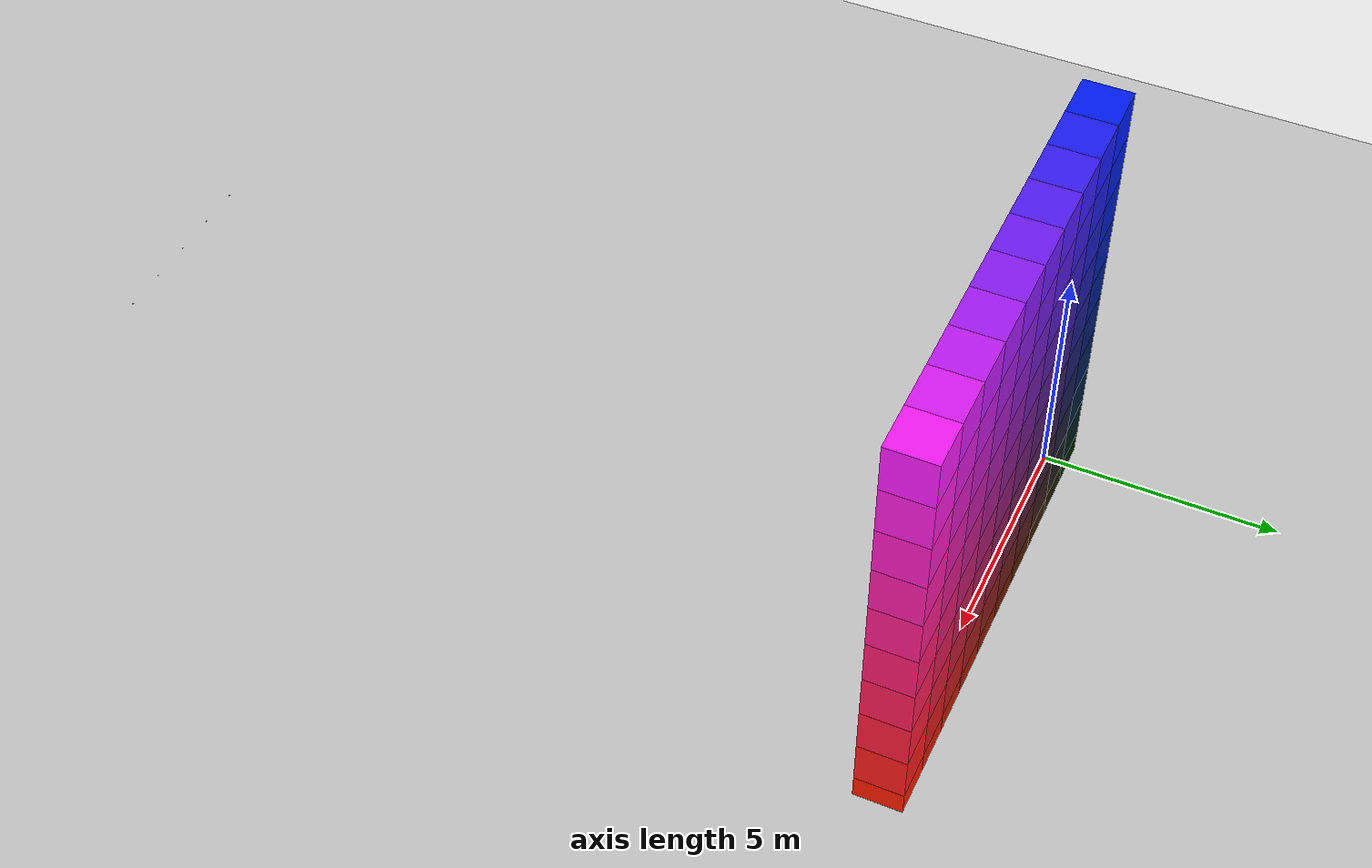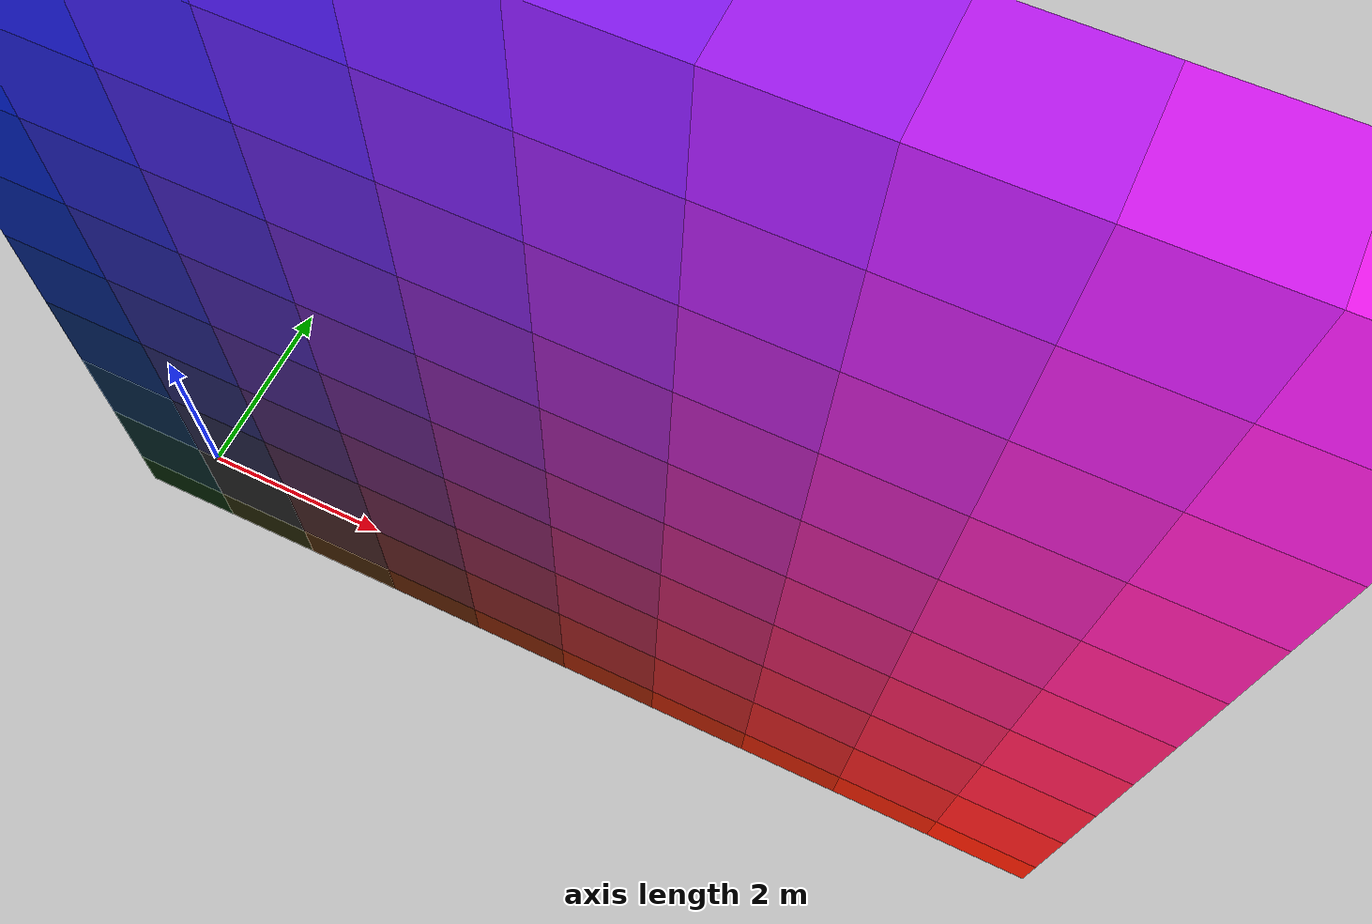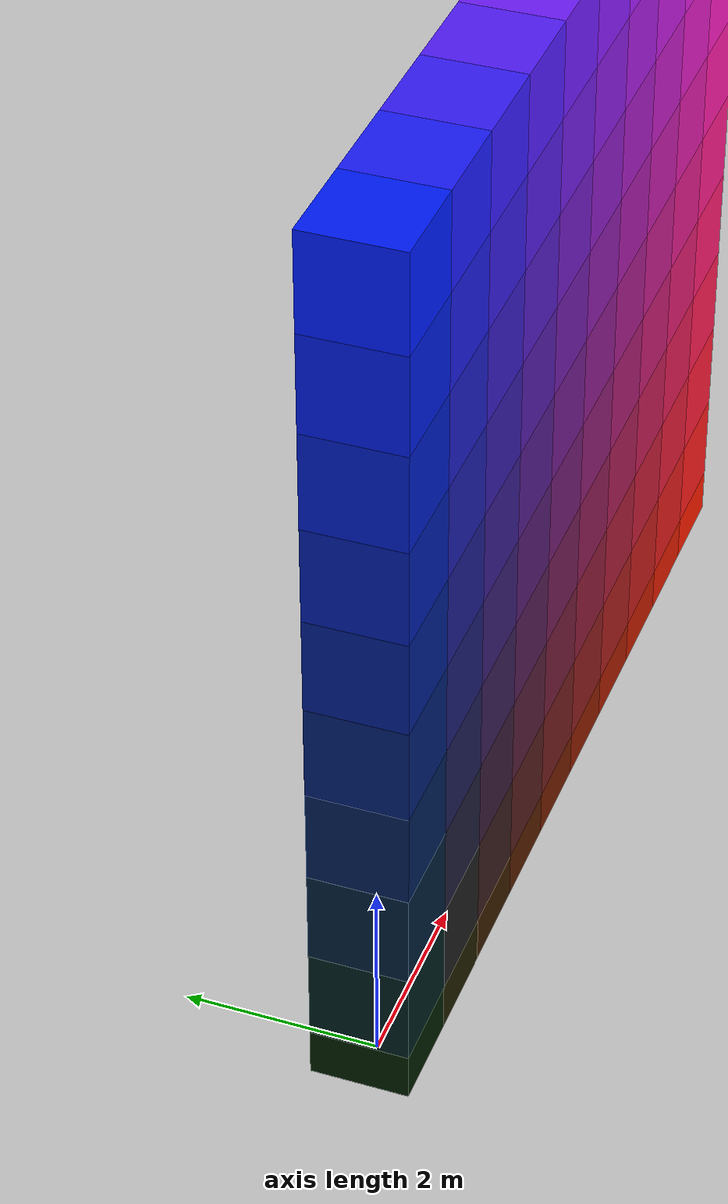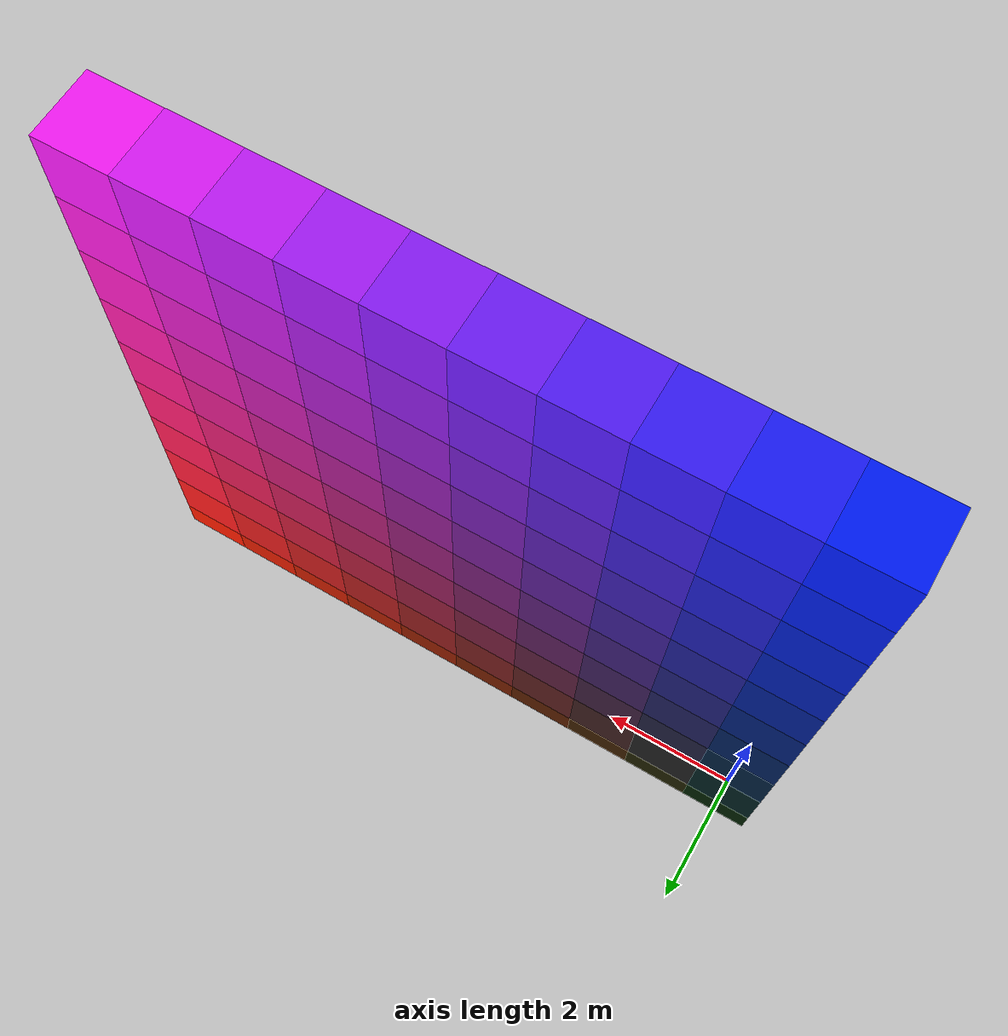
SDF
<?xml version="1.0" ?>

<sdf version="1.6">
  <world name="default">
    <physics name="1ms" type="ode">
      <max_step_size>0.001</max_step_size>
      <real_time_factor>1.0</real_time_factor>
    </physics>

    <plugin
      filename="libignition-gazebo-physics-system.so"
      name="ignition::gazebo::systems::Physics">
    </plugin>
    <plugin
      filename="libignition-gazebo-user-commands-system.so"
      name="ignition::gazebo::systems::UserCommands">
    </plugin>
    <plugin
      filename="libignition-gazebo-scene-broadcaster-system.so"
      name="ignition::gazebo::systems::SceneBroadcaster">
    </plugin>
    <plugin
      filename="libignition-gazebo-sensors-system.so"
      name="ignition::gazebo::systems::Sensors">
        <render_engine>ogre2</render_engine>
    </plugin>

    <gui fullscreen="0">

      <!-- 3D scene -->
      <plugin filename="GzScene3D" name="3D View">
        <ignition-gui>
          <title>3D View</title>
          <property type="bool" key="showTitleBar">false</property>
          <property type="string" key="state">docked</property>
        </ignition-gui>

        <engine>ogre2</engine>
        <scene>scene</scene>
        <ambient_light>1.0 1.0 1.0</ambient_light>
        <background_color>0.8 0.8 0.8</background_color>
        <camera_pose>-6 0 6 0 0.5 0</camera_pose>
      </plugin>

      <!-- World control -->
      <plugin filename="WorldControl" name="World control">
        <ignition-gui>
          <title>World control</title>
          <property type="bool" key="showTitleBar">false</property>
          <property type="bool" key="resizable">false</property>
          <property type="double" key="height">72</property>
          <property type="double" key="width">121</property>
          <property type="double" key="z">1</property>

          <property type="string" key="state">floating</property>
          <anchors target="3D View">
            <line own="left" target="left"/>
            <line own="bottom" target="bottom"/>
          </anchors>
        </ignition-gui>

        <play_pause>true</play_pause>
        <step>true</step>
        <start_paused>true</start_paused>
        <service>/world/default/control</service>
        <stats_topic>/world/default/stats</stats_topic>

      </plugin>

      <!-- World statistics -->
      <plugin filename="WorldStats" name="World stats">
        <ignition-gui>
          <title>World stats</title>
          <property type="bool" key="showTitleBar">false</property>
          <property type="bool" key="resizable">false</property>
          <property type="double" key="height">110</property>
          <property type="double" key="width">290</property>
          <property type="double" key="z">1</property>

          <property type="string" key="state">floating</property>
          <anchors target="3D View">
            <line own="right" target="right"/>
            <line own="bottom" target="bottom"/>
          </anchors>
        </ignition-gui>

        <sim_time>true</sim_time>
        <real_time>true</real_time>
        <real_time_factor>true</real_time_factor>
        <iterations>true</iterations>
        <topic>/world/default/stats</topic>
      </plugin>
    </gui>

    <light type="directional" name="sun">
      <cast_shadows>true</cast_shadows>
      <pose>0 0 10 0 0 0</pose>
      <diffuse>0.8 0.8 0.8 1</diffuse>
      <specular>0.2 0.2 0.2 1</specular>
      <attenuation>
        <range>1000</range>
        <constant>0.9</constant>
        <linear>0.01</linear>
        <quadratic>0.001</quadratic>
      </attenuation>
      <direction>-0.5 0.1 -0.9</direction>
    </light>

    <model name="ground_plane">
      <static>true</static>
      <link name="link">
        <collision name="collision">
          <geometry>
            <plane>
              <normal>0 0 1</normal>
            </plane>
          </geometry>
        </collision>
        <visual name="visual">
          <geometry>
            <plane>
              <normal>0 0 1</normal>
              <size>100 100</size>
            </plane>
          </geometry>
          <material>
            <ambient>0.8 0.8 0.8 1</ambient>
            <diffuse>0.8 0.8 0.8 1</diffuse>
            <specular>0.8 0.8 0.8 1</specular>
          </material>
        </visual>
      </link>
    </model>

    <model name="camera_0">
      <static>true</static>
      <pose>0.0 -20 0 0 0 1.5707</pose>
      <link name="base_link">
        <visual name="camera_visual">
            <pose>0.0 0 0.0 0 0 0</pose>
            <geometry>
                <box>
                    <size>0.02 0.02 0.02</size>
                </box>
            </geometry>
        </visual>
        <sensor name="camera_sensor_0" type="camera">
            <pose>0.0 0 0.0 0 0 0</pose>
            <always_on>1</always_on>
            <update_rate>50</update_rate>
            <camera name="camera_front">
                <pose frame="">0 0 0 0 -1.5707 1.5707</pose>
                <horizontal_fov>1.0472</horizontal_fov>
                <distortion>
                    <k1>0.0</k1>
                    <k2>0.0</k2>
                    <k3>0.0</k3>
                    <p1>0.0</p1>
                    <p2>0.0</p2>
                    <center>0.5 0.5</center>
                </distortion>
                <image>
                    <width>1280</width>
                    <height>960</height>
                    <format>R8G8B8</format>
                </image>
                <clip>
                    <near>0.01</near>
                    <far>300</far>
                </clip>
                <noise>
                    <type>gaussian</type>
                    <mean>0</mean>
                    <stddev>0.007</stddev>
                </noise>
            </camera>
        </sensor>
      </link>
    </model>

    <model name="camera_1">
      <static>true</static>
      <pose>1.0 -20 0 0 0 1.5707</pose>
      <link name="base_link">
        <visual name="camera_visual">
            <pose>0.0 0 0.0 0 0 0</pose>
            <geometry>
                <box>
                    <size>0.02 0.02 0.02</size>
                </box>
            </geometry>
        </visual>
        <sensor name="camera_sensor_1" type="camera">
            <pose>0.0 0 0.0 0 0 0</pose>
            <always_on>1</always_on>
            <update_rate>50</update_rate>
            <camera name="camera_front">
                <pose frame="">0 0 0 0 -1.5707 1.5707</pose>
                <horizontal_fov>1.0472</horizontal_fov>
                <distortion>
                    <k1>0.0</k1>
                    <k2>0.0</k2>
                    <k3>0.0</k3>
                    <p1>0.0</p1>
                    <p2>0.0</p2>
                    <center>0.5 0.5</center>
                </distortion>
                <image>
                    <width>1280</width>
                    <height>960</height>
                    <format>R8G8B8</format>
                </image>
                <clip>
                    <near>0.01</near>
                    <far>300</far>
                </clip>
                <noise>
                    <type>gaussian</type>
                    <mean>0</mean>
                    <stddev>0.007</stddev>
                </noise>
            </camera>
        </sensor>
      </link>
    </model>

    <model name="camera_2">
      <static>true</static>
      <pose>2.0 -20 0 0 0 1.5707</pose>
      <link name="base_link">
        <visual name="camera_visual">
            <pose>0.0 0 0.0 0 0 0</pose>
            <geometry>
                <box>
                    <size>0.02 0.02 0.02</size>
                </box>
            </geometry>
        </visual>
        <sensor name="camera_sensor_2" type="camera">
            <pose>0.0 0 0.0 0 0 0</pose>
            <always_on>1</always_on>
            <update_rate>50</update_rate>
            <camera name="camera_front">
                <pose frame="">0 0 0 0 -1.5707 1.5707</pose>
                <horizontal_fov>1.0472</horizontal_fov>
                <distortion>
                    <k1>0.0</k1>
                    <k2>0.0</k2>
                    <k3>0.0</k3>
                    <p1>0.0</p1>
                    <p2>0.0</p2>
                    <center>0.5 0.5</center>
                </distortion>
                <image>
                    <width>1280</width>
                    <height>960</height>
                    <format>R8G8B8</format>
                </image>
                <clip>
                    <near>0.01</near>
                    <far>300</far>
                </clip>
                <noise>
                    <type>gaussian</type>
                    <mean>0</mean>
                    <stddev>0.007</stddev>
                </noise>
            </camera>
        </sensor>
      </link>
    </model>

    <model name="camera_3">
      <static>true</static>
      <pose>3.0 -20 0 0 0 1.5707</pose>
      <link name="base_link">
        <visual name="camera_visual">
            <pose>0.0 0 0.0 0 0 0</pose>
            <geometry>
                <box>
                    <size>0.02 0.02 0.02</size>
                </box>
            </geometry>
        </visual>
        <sensor name="camera_sensor_3" type="camera">
            <pose>0.0 0 0.0 0 0 0</pose>
            <always_on>1</always_on>
            <update_rate>50</update_rate>
            <camera name="camera_front">
                <pose frame="">0 0 0 0 -1.5707 1.5707</pose>
                <horizontal_fov>1.0472</horizontal_fov>
                <distortion>
                    <k1>0.0</k1>
                    <k2>0.0</k2>
                    <k3>0.0</k3>
                    <p1>0.0</p1>
                    <p2>0.0</p2>
                    <center>0.5 0.5</center>
                </distortion>
                <image>
                    <width>1280</width>
                    <height>960</height>
                    <format>R8G8B8</format>
                </image>
                <clip>
                    <near>0.01</near>
                    <far>300</far>
                </clip>
                <noise>
                    <type>gaussian</type>
                    <mean>0</mean>
                    <stddev>0.007</stddev>
                </noise>
            </camera>
        </sensor>
      </link>
    </model>

    <model name="camera_4">
      <static>true</static>
      <pose>4.0 -20 0 0 0 1.5707</pose>
      <link name="base_link">
        <visual name="camera_visual">
            <pose>0.0 0 0.0 0 0 0</pose>
            <geometry>
                <box>
                    <size>0.02 0.02 0.02</size>
                </box>
            </geometry>
        </visual>
        <sensor name="camera_sensor_4" type="camera">
            <pose>0.0 0 0.0 0 0 0</pose>
            <always_on>1</always_on>
            <update_rate>50</update_rate>
            <camera name="camera_front">
                <pose frame="">0 0 0 0 -1.5707 1.5707</pose>
                <horizontal_fov>1.0472</horizontal_fov>
                <distortion>
                    <k1>0.0</k1>
                    <k2>0.0</k2>
                    <k3>0.0</k3>
                    <p1>0.0</p1>
                    <p2>0.0</p2>
                    <center>0.5 0.5</center>
                </distortion>
                <image>
                    <width>1280</width>
                    <height>960</height>
                    <format>R8G8B8</format>
                </image>
                <clip>
                    <near>0.01</near>
                    <far>300</far>
                </clip>
                <noise>
                    <type>gaussian</type>
                    <mean>0</mean>
                    <stddev>0.007</stddev>
                </noise>
            </camera>
        </sensor>
      </link>
    </model>

    <model name="model_0_1.0_0">
      <static>true</static>
      <pose>
        0.0
        0.0
        0.0
        0.0
        0.0
        0.0
      </pose>
      <link name="box_link">
        <inertial>
          <inertia>
            <ixx>1</ixx>
            <ixy>0</ixy>
            <ixz>0</ixz>
            <iyy>1</iyy>
            <iyz>0</iyz>
            <izz>1</izz>
          </inertia>
          <mass>5.0</mass>
        </inertial>
        <collision name="box_collision">
          <geometry>
            <box>
              <size>1 1 1</size>
            </box>
          </geometry>
        </collision>
        <visual name="box_visual">
          <geometry>
            <box>
              <size>1 1 1</size>
            </box>
          </geometry>
          <material>
            <ambient>
              0.0
              0.1111111111111111
              0.0
              1
            </ambient>
            <diffuse>
              0.0
              0.1111111111111111
              0.0
              1
            </diffuse>
            <specular>
              0.0
              0.1111111111111111
              0.0
              1
            </specular>
          </material>
        </visual>
      </link>
    </model>

    <model name="model_0_1.0_1">
      <static>true</static>
      <pose>
        0.0
        0.0
        1.0
        0.0
        0.0
        0.0
      </pose>
      <link name="box_link">
        <inertial>
          <inertia>
            <ixx>1</ixx>
            <ixy>0</ixy>
            <ixz>0</ixz>
            <iyy>1</iyy>
            <iyz>0</iyz>
            <izz>1</izz>
          </inertia>
          <mass>5.0</mass>
        </inertial>
        <collision name="box_collision">
          <geometry>
            <box>
              <size>1 1 1</size>
            </box>
          </geometry>
        </collision>
        <visual name="box_visual">
          <geometry>
            <box>
              <size>1 1 1</size>
            </box>
          </geometry>
          <material>
            <ambient>
              0.0
              0.1111111111111111
              0.1111111111111111
              1
            </ambient>
            <diffuse>
              0.0
              0.1111111111111111
              0.1111111111111111
              1
            </diffuse>
            <specular>
              0.0
              0.1111111111111111
              0.1111111111111111
              1
            </specular>
          </material>
        </visual>
      </link>
    </model>

    <model name="model_0_1.0_2">
      <static>true</static>
      <pose>
        0.0
        0.0
        2.0
        0.0
        0.0
        0.0
      </pose>
      <link name="box_link">
        <inertial>
          <inertia>
            <ixx>1</ixx>
            <ixy>0</ixy>
            <ixz>0</ixz>
            <iyy>1</iyy>
            <iyz>0</iyz>
            <izz>1</izz>
          </inertia>
          <mass>5.0</mass>
        </inertial>
        <collision name="box_collision">
          <geometry>
            <box>
              <size>1 1 1</size>
            </box>
          </geometry>
        </collision>
        <visual name="box_visual">
          <geometry>
            <box>
              <size>1 1 1</size>
            </box>
          </geometry>
          <material>
            <ambient>
              0.0
              0.1111111111111111
              0.2222222222222222
              1
            </ambient>
            <diffuse>
              0.0
              0.1111111111111111
              0.2222222222222222
              1
            </diffuse>
            <specular>
              0.0
              0.1111111111111111
              0.2222222222222222
              1
            </specular>
          </material>
        </visual>
      </link>
    </model>

    <model name="model_0_1.0_3">
      <static>true</static>
      <pose>
        0.0
        0.0
        3.0
        0.0
        0.0
        0.0
      </pose>
      <link name="box_link">
        <inertial>
          <inertia>
            <ixx>1</ixx>
            <ixy>0</ixy>
            <ixz>0</ixz>
            <iyy>1</iyy>
            <iyz>0</iyz>
            <izz>1</izz>
          </inertia>
          <mass>5.0</mass>
        </inertial>
        <collision name="box_collision">
          <geometry>
            <box>
              <size>1 1 1</size>
            </box>
          </geometry>
        </collision>
        <visual name="box_visual">
          <geometry>
            <box>
              <size>1 1 1</size>
            </box>
          </geometry>
          <material>
            <ambient>
              0.0
              0.1111111111111111
              0.3333333333333333
              1
            </ambient>
            <diffuse>
              0.0
              0.1111111111111111
              0.3333333333333333
              1
            </diffuse>
            <specular>
              0.0
              0.1111111111111111
              0.3333333333333333
              1
            </specular>
          </material>
        </visual>
      </link>
    </model>

    <model name="model_0_1.0_4">
      <static>true</static>
      <pose>
        0.0
        0.0
        4.0
        0.0
        0.0
        0.0
      </pose>
      <link name="box_link">
        <inertial>
          <inertia>
            <ixx>1</ixx>
            <ixy>0</ixy>
            <ixz>0</ixz>
            <iyy>1</iyy>
            <iyz>0</iyz>
            <izz>1</izz>
          </inertia>
          <mass>5.0</mass>
        </inertial>
        <collision name="box_collision">
          <geometry>
            <box>
              <size>1 1 1</size>
            </box>
          </geometry>
        </collision>
        <visual name="box_visual">
          <geometry>
            <box>
              <size>1 1 1</size>
            </box>
          </geometry>
          <material>
            <ambient>
              0.0
              0.1111111111111111
              0.4444444444444444
              1
            </ambient>
            <diffuse>
              0.0
              0.1111111111111111
              0.4444444444444444
              1
            </diffuse>
            <specular>
              0.0
              0.1111111111111111
              0.4444444444444444
              1
            </specular>
          </material>
        </visual>
      </link>
    </model>

    <model name="model_0_1.0_5">
      <static>true</static>
      <pose>
        0.0
        0.0
        5.0
        0.0
        0.0
        0.0
      </pose>
      <link name="box_link">
        <inertial>
          <inertia>
            <ixx>1</ixx>
            <ixy>0</ixy>
            <ixz>0</ixz>
            <iyy>1</iyy>
            <iyz>0</iyz>
            <izz>1</izz>
          </inertia>
          <mass>5.0</mass>
        </inertial>
        <collision name="box_collision">
          <geometry>
            <box>
              <size>1 1 1</size>
            </box>
          </geometry>
        </collision>
        <visual name="box_visual">
          <geometry>
            <box>
              <size>1 1 1</size>
            </box>
          </geometry>
          <material>
            <ambient>
              0.0
              0.1111111111111111
              0.5555555555555556
              1
            </ambient>
            <diffuse>
              0.0
              0.1111111111111111
              0.5555555555555556
              1
            </diffuse>
            <specular>
              0.0
              0.1111111111111111
              0.5555555555555556
              1
            </specular>
          </material>
        </visual>
      </link>
    </model>

    <model name="model_0_1.0_6">
      <static>true</static>
      <pose>
        0.0
        0.0
        6.0
        0.0
        0.0
        0.0
      </pose>
      <link name="box_link">
        <inertial>
          <inertia>
            <ixx>1</ixx>
            <ixy>0</ixy>
            <ixz>0</ixz>
            <iyy>1</iyy>
            <iyz>0</iyz>
            <izz>1</izz>
          </inertia>
          <mass>5.0</mass>
        </inertial>
        <collision name="box_collision">
          <geometry>
            <box>
              <size>1 1 1</size>
            </box>
          </geometry>
        </collision>
        <visual name="box_visual">
          <geometry>
            <box>
              <size>1 1 1</size>
            </box>
          </geometry>
          <material>
            <ambient>
              0.0
              0.1111111111111111
              0.6666666666666666
              1
            </ambient>
            <diffuse>
              0.0
              0.1111111111111111
              0.6666666666666666
              1
            </diffuse>
            <specular>
              0.0
              0.1111111111111111
              0.6666666666666666
              1
            </specular>
          </material>
        </visual>
      </link>
    </model>

    <model name="model_0_1.0_7">
      <static>true</static>
      <pose>
        0.0
        0.0
        7.0
        0.0
        0.0
        0.0
      </pose>
      <link name="box_link">
        <inertial>
          <inertia>
            <ixx>1</ixx>
            <ixy>0</ixy>
            <ixz>0</ixz>
            <iyy>1</iyy>
            <iyz>0</iyz>
            <izz>1</izz>
          </inertia>
          <mass>5.0</mass>
        </inertial>
        <collision name="box_collision">
          <geometry>
            <box>
              <size>1 1 1</size>
            </box>
          </geometry>
        </collision>
        <visual name="box_visual">
          <geometry>
            <box>
              <size>1 1 1</size>
            </box>
          </geometry>
          <material>
            <ambient>
              0.0
              0.1111111111111111
              0.7777777777777778
              1
            </ambient>
            <diffuse>
              0.0
              0.1111111111111111
              0.7777777777777778
              1
            </diffuse>
            <specular>
              0.0
              0.1111111111111111
              0.7777777777777778
              1
            </specular>
          </material>
        </visual>
      </link>
    </model>

    <model name="model_0_1.0_8">
      <static>true</static>
      <pose>
        0.0
        0.0
        8.0
        0.0
        0.0
        0.0
      </pose>
      <link name="box_link">
        <inertial>
          <inertia>
            <ixx>1</ixx>
            <ixy>0</ixy>
            <ixz>0</ixz>
            <iyy>1</iyy>
            <iyz>0</iyz>
            <izz>1</izz>
          </inertia>
          <mass>5.0</mass>
        </inertial>
        <collision name="box_collision">
          <geometry>
            <box>
              <size>1 1 1</size>
            </box>
          </geometry>
        </collision>
        <visual name="box_visual">
          <geometry>
            <box>
              <size>1 1 1</size>
            </box>
          </geometry>
          <material>
            <ambient>
              0.0
              0.1111111111111111
              0.8888888888888888
              1
            </ambient>
            <diffuse>
              0.0
              0.1111111111111111
              0.8888888888888888
              1
            </diffuse>
            <specular>
              0.0
              0.1111111111111111
              0.8888888888888888
              1
            </specular>
          </material>
        </visual>
      </link>
    </model>

    <model name="model_0_1.0_9">
      <static>true</static>
      <pose>
        0.0
        0.0
        9.0
        0.0
        0.0
        0.0
      </pose>
      <link name="box_link">
        <inertial>
          <inertia>
            <ixx>1</ixx>
            <ixy>0</ixy>
            <ixz>0</ixz>
            <iyy>1</iyy>
            <iyz>0</iyz>
            <izz>1</izz>
          </inertia>
          <mass>5.0</mass>
        </inertial>
        <collision name="box_collision">
          <geometry>
            <box>
              <size>1 1 1</size>
            </box>
          </geometry>
        </collision>
        <visual name="box_visual">
          <geometry>
            <box>
              <size>1 1 1</size>
            </box>
          </geometry>
          <material>
            <ambient>
              0.0
              0.1111111111111111
              1.0
              1
            </ambient>
            <diffuse>
              0.0
              0.1111111111111111
              1.0
              1
            </diffuse>
            <specular>
              0.0
              0.1111111111111111
              1.0
              1
            </specular>
          </material>
        </visual>
      </link>
    </model>

    <model name="model_1_1.0_0">
      <static>true</static>
      <pose>
        1.0
        0.0
        0.0
        0.0
        0.0
        0.0
      </pose>
      <link name="box_link">
        <inertial>
          <inertia>
            <ixx>1</ixx>
            <ixy>0</ixy>
            <ixz>0</ixz>
            <iyy>1</iyy>
            <iyz>0</iyz>
            <izz>1</izz>
          </inertia>
          <mass>5.0</mass>
        </inertial>
        <collision name="box_collision">
          <geometry>
            <box>
              <size>1 1 1</size>
            </box>
          </geometry>
        </collision>
        <visual name="box_visual">
          <geometry>
            <box>
              <size>1 1 1</size>
            </box>
          </geometry>
          <material>
            <ambient>
              0.1111111111111111
              0.1111111111111111
              0.0
              1
            </ambient>
            <diffuse>
              0.1111111111111111
              0.1111111111111111
              0.0
              1
            </diffuse>
            <specular>
              0.1111111111111111
              0.1111111111111111
              0.0
              1
            </specular>
          </material>
        </visual>
      </link>
    </model>

    <model name="model_1_1.0_1">
      <static>true</static>
      <pose>
        1.0
        0.0
        1.0
        0.0
        0.0
        0.0
      </pose>
      <link name="box_link">
        <inertial>
          <inertia>
            <ixx>1</ixx>
            <ixy>0</ixy>
            <ixz>0</ixz>
            <iyy>1</iyy>
            <iyz>0</iyz>
            <izz>1</izz>
          </inertia>
          <mass>5.0</mass>
        </inertial>
        <collision name="box_collision">
          <geometry>
            <box>
              <size>1 1 1</size>
            </box>
          </geometry>
        </collision>
        <visual name="box_visual">
          <geometry>
            <box>
              <size>1 1 1</size>
            </box>
          </geometry>
          <material>
            <ambient>
              0.1111111111111111
              0.1111111111111111
              0.1111111111111111
              1
            </ambient>
            <diffuse>
              0.1111111111111111
              0.1111111111111111
              0.1111111111111111
              1
            </diffuse>
            <specular>
              0.1111111111111111
              0.1111111111111111
              0.1111111111111111
              1
            </specular>
          </material>
        </visual>
      </link>
    </model>

    <model name="model_1_1.0_2">
      <static>true</static>
      <pose>
        1.0
        0.0
        2.0
        0.0
        0.0
        0.0
      </pose>
      <link name="box_link">
        <inertial>
          <inertia>
            <ixx>1</ixx>
            <ixy>0</ixy>
            <ixz>0</ixz>
            <iyy>1</iyy>
            <iyz>0</iyz>
            <izz>1</izz>
          </inertia>
          <mass>5.0</mass>
        </inertial>
        <collision name="box_collision">
          <geometry>
            <box>
              <size>1 1 1</size>
            </box>
          </geometry>
        </collision>
        <visual name="box_visual">
          <geometry>
            <box>
              <size>1 1 1</size>
            </box>
          </geometry>
          <material>
            <ambient>
              0.1111111111111111
              0.1111111111111111
              0.2222222222222222
              1
            </ambient>
            <diffuse>
              0.1111111111111111
              0.1111111111111111
              0.2222222222222222
              1
            </diffuse>
            <specular>
              0.1111111111111111
              0.1111111111111111
              0.2222222222222222
              1
            </specular>
          </material>
        </visual>
      </link>
    </model>

    <model name="model_1_1.0_3">
      <static>true</static>
      <pose>
        1.0
        0.0
        3.0
        0.0
        0.0
        0.0
      </pose>
      <link name="box_link">
        <inertial>
          <inertia>
            <ixx>1</ixx>
            <ixy>0</ixy>
            <ixz>0</ixz>
            <iyy>1</iyy>
            <iyz>0</iyz>
            <izz>1</izz>
          </inertia>
          <mass>5.0</mass>
        </inertial>
        <collision name="box_collision">
          <geometry>
            <box>
              <size>1 1 1</size>
            </box>
          </geometry>
        </collision>
        <visual name="box_visual">
          <geometry>
            <box>
              <size>1 1 1</size>
            </box>
          </geometry>
          <material>
            <ambient>
              0.1111111111111111
              0.1111111111111111
              0.3333333333333333
              1
            </ambient>
            <diffuse>
              0.1111111111111111
              0.1111111111111111
              0.3333333333333333
              1
            </diffuse>
            <specular>
              0.1111111111111111
              0.1111111111111111
              0.3333333333333333
              1
            </specular>
          </material>
        </visual>
      </link>
    </model>

    <model name="model_1_1.0_4">
      <static>true</static>
      <pose>
        1.0
        0.0
        4.0
        0.0
        0.0
        0.0
      </pose>
      <link name="box_link">
        <inertial>
          <inertia>
            <ixx>1</ixx>
            <ixy>0</ixy>
            <ixz>0</ixz>
            <iyy>1</iyy>
            <iyz>0</iyz>
            <izz>1</izz>
          </inertia>
          <mass>5.0</mass>
        </inertial>
        <collision name="box_collision">
          <geometry>
            <box>
              <size>1 1 1</size>
            </box>
          </geometry>
        </collision>
        <visual name="box_visual">
          <geometry>
            <box>
              <size>1 1 1</size>
            </box>
          </geometry>
          <material>
            <ambient>
              0.1111111111111111
              0.1111111111111111
              0.4444444444444444
              1
            </ambient>
            <diffuse>
              0.1111111111111111
              0.1111111111111111
              0.4444444444444444
              1
            </diffuse>
            <specular>
              0.1111111111111111
              0.1111111111111111
              0.4444444444444444
              1
            </specular>
          </material>
        </visual>
      </link>
    </model>

    <model name="model_1_1.0_5">
      <static>true</static>
      <pose>
        1.0
        0.0
        5.0
        0.0
        0.0
        0.0
      </pose>
      <link name="box_link">
        <inertial>
          <inertia>
            <ixx>1</ixx>
            <ixy>0</ixy>
            <ixz>0</ixz>
            <iyy>1</iyy>
            <iyz>0</iyz>
            <izz>1</izz>
          </inertia>
          <mass>5.0</mass>
        </inertial>
        <collision name="box_collision">
          <geometry>
            <box>
              <size>1 1 1</size>
            </box>
          </geometry>
        </collision>
        <visual name="box_visual">
          <geometry>
            <box>
              <size>1 1 1</size>
            </box>
          </geometry>
          <material>
            <ambient>
              0.1111111111111111
              0.1111111111111111
              0.5555555555555556
              1
            </ambient>
            <diffuse>
              0.1111111111111111
              0.1111111111111111
              0.5555555555555556
              1
            </diffuse>
            <specular>
              0.1111111111111111
              0.1111111111111111
              0.5555555555555556
              1
            </specular>
          </material>
        </visual>
      </link>
    </model>

    <model name="model_1_1.0_6">
      <static>true</static>
      <pose>
        1.0
        0.0
        6.0
        0.0
        0.0
        0.0
      </pose>
      <link name="box_link">
        <inertial>
          <inertia>
            <ixx>1</ixx>
            <ixy>0</ixy>
            <ixz>0</ixz>
            <iyy>1</iyy>
            <iyz>0</iyz>
            <izz>1</izz>
          </inertia>
          <mass>5.0</mass>
        </inertial>
        <collision name="box_collision">
          <geometry>
            <box>
              <size>1 1 1</size>
            </box>
          </geometry>
        </collision>
        <visual name="box_visual">
          <geometry>
            <box>
              <size>1 1 1</size>
            </box>
          </geometry>
          <material>
            <ambient>
              0.1111111111111111
              0.1111111111111111
              0.6666666666666666
              1
            </ambient>
            <diffuse>
              0.1111111111111111
              0.1111111111111111
              0.6666666666666666
              1
            </diffuse>
            <specular>
              0.1111111111111111
              0.1111111111111111
              0.6666666666666666
              1
            </specular>
          </material>
        </visual>
      </link>
    </model>

    <model name="model_1_1.0_7">
      <static>true</static>
      <pose>
        1.0
        0.0
        7.0
        0.0
        0.0
        0.0
      </pose>
      <link name="box_link">
        <inertial>
          <inertia>
            <ixx>1</ixx>
            <ixy>0</ixy>
            <ixz>0</ixz>
            <iyy>1</iyy>
            <iyz>0</iyz>
            <izz>1</izz>
          </inertia>
          <mass>5.0</mass>
        </inertial>
        <collision name="box_collision">
          <geometry>
            <box>
              <size>1 1 1</size>
            </box>
          </geometry>
        </collision>
        <visual name="box_visual">
          <geometry>
            <box>
              <size>1 1 1</size>
            </box>
          </geometry>
          <material>
            <ambient>
              0.1111111111111111
              0.1111111111111111
              0.7777777777777778
              1
            </ambient>
            <diffuse>
              0.1111111111111111
              0.1111111111111111
              0.7777777777777778
              1
            </diffuse>
            <specular>
              0.1111111111111111
              0.1111111111111111
              0.7777777777777778
              1
            </specular>
          </material>
        </visual>
      </link>
    </model>

    <model name="model_1_1.0_8">
      <static>true</static>
      <pose>
        1.0
        0.0
        8.0
        0.0
        0.0
        0.0
      </pose>
      <link name="box_link">
        <inertial>
          <inertia>
            <ixx>1</ixx>
            <ixy>0</ixy>
            <ixz>0</ixz>
            <iyy>1</iyy>
            <iyz>0</iyz>
            <izz>1</izz>
          </inertia>
          <mass>5.0</mass>
        </inertial>
        <collision name="box_collision">
          <geometry>
            <box>
              <size>1 1 1</size>
            </box>
          </geometry>
        </collision>
        <visual name="box_visual">
          <geometry>
            <box>
              <size>1 1 1</size>
            </box>
          </geometry>
          <material>
            <ambient>
              0.1111111111111111
              0.1111111111111111
              0.8888888888888888
              1
            </ambient>
            <diffuse>
              0.1111111111111111
              0.1111111111111111
              0.8888888888888888
              1
            </diffuse>
            <specular>
              0.1111111111111111
              0.1111111111111111
              0.8888888888888888
              1
            </specular>
          </material>
        </visual>
      </link>
    </model>

    <model name="model_1_1.0_9">
      <static>true</static>
      <pose>
        1.0
        0.0
        9.0
        0.0
        0.0
        0.0
      </pose>
      <link name="box_link">
        <inertial>
          <inertia>
            <ixx>1</ixx>
            <ixy>0</ixy>
            <ixz>0</ixz>
            <iyy>1</iyy>
            <iyz>0</iyz>
            <izz>1</izz>
          </inertia>
          <mass>5.0</mass>
        </inertial>
        <collision name="box_collision">
          <geometry>
            <box>
              <size>1 1 1</size>
            </box>
          </geometry>
        </collision>
        <visual name="box_visual">
          <geometry>
            <box>
              <size>1 1 1</size>
            </box>
          </geometry>
          <material>
            <ambient>
              0.1111111111111111
              0.1111111111111111
              1.0
              1
            </ambient>
            <diffuse>
              0.1111111111111111
              0.1111111111111111
              1.0
              1
            </diffuse>
            <specular>
              0.1111111111111111
              0.1111111111111111
              1.0
              1
            </specular>
          </material>
        </visual>
      </link>
    </model>

    <model name="model_2_1.0_0">
      <static>true</static>
      <pose>
        2.0
        0.0
        0.0
        0.0
        0.0
        0.0
      </pose>
      <link name="box_link">
        <inertial>
          <inertia>
            <ixx>1</ixx>
            <ixy>0</ixy>
            <ixz>0</ixz>
            <iyy>1</iyy>
            <iyz>0</iyz>
            <izz>1</izz>
          </inertia>
          <mass>5.0</mass>
        </inertial>
        <collision name="box_collision">
          <geometry>
            <box>
              <size>1 1 1</size>
            </box>
          </geometry>
        </collision>
        <visual name="box_visual">
          <geometry>
            <box>
              <size>1 1 1</size>
            </box>
          </geometry>
          <material>
            <ambient>
              0.2222222222222222
              0.1111111111111111
              0.0
              1
            </ambient>
            <diffuse>
              0.2222222222222222
              0.1111111111111111
              0.0
              1
            </diffuse>
            <specular>
              0.2222222222222222
              0.1111111111111111
              0.0
              1
            </specular>
          </material>
        </visual>
      </link>
    </model>

    <model name="model_2_1.0_1">
      <static>true</static>
      <pose>
        2.0
        0.0
        1.0
        0.0
        0.0
        0.0
      </pose>
      <link name="box_link">
        <inertial>
          <inertia>
            <ixx>1</ixx>
            <ixy>0</ixy>
            <ixz>0</ixz>
            <iyy>1</iyy>
            <iyz>0</iyz>
            <izz>1</izz>
          </inertia>
          <mass>5.0</mass>
        </inertial>
        <collision name="box_collision">
          <geometry>
            <box>
              <size>1 1 1</size>
            </box>
          </geometry>
        </collision>
        <visual name="box_visual">
          <geometry>
            <box>
              <size>1 1 1</size>
            </box>
          </geometry>
          <material>
            <ambient>
              0.2222222222222222
              0.1111111111111111
              0.1111111111111111
              1
            </ambient>
            <diffuse>
              0.2222222222222222
              0.1111111111111111
              0.1111111111111111
              1
            </diffuse>
            <specular>
              0.2222222222222222
              0.1111111111111111
              0.1111111111111111
              1
            </specular>
          </material>
        </visual>
      </link>
    </model>

    <model name="model_2_1.0_2">
      <static>true</static>
      <pose>
        2.0
        0.0
        2.0
        0.0
        0.0
        0.0
      </pose>
      <link name="box_link">
        <inertial>
          <inertia>
            <ixx>1</ixx>
            <ixy>0</ixy>
            <ixz>0</ixz>
            <iyy>1</iyy>
            <iyz>0</iyz>
            <izz>1</izz>
          </inertia>
          <mass>5.0</mass>
        </inertial>
        <collision name="box_collision">
          <geometry>
            <box>
              <size>1 1 1</size>
            </box>
          </geometry>
        </collision>
        <visual name="box_visual">
          <geometry>
            <box>
              <size>1 1 1</size>
            </box>
          </geometry>
          <material>
            <ambient>
              0.2222222222222222
              0.1111111111111111
              0.2222222222222222
              1
            </ambient>
            <diffuse>
              0.2222222222222222
              0.1111111111111111
              0.2222222222222222
              1
            </diffuse>
            <specular>
              0.2222222222222222
              0.1111111111111111
              0.2222222222222222
              1
            </specular>
          </material>
        </visual>
      </link>
    </model>

    <model name="model_2_1.0_3">
      <static>true</static>
      <pose>
        2.0
        0.0
        3.0
        0.0
        0.0
        0.0
      </pose>
      <link name="box_link">
        <inertial>
          <inertia>
            <ixx>1</ixx>
            <ixy>0</ixy>
            <ixz>0</ixz>
            <iyy>1</iyy>
            <iyz>0</iyz>
            <izz>1</izz>
          </inertia>
          <mass>5.0</mass>
        </inertial>
        <collision name="box_collision">
          <geometry>
            <box>
              <size>1 1 1</size>
            </box>
          </geometry>
        </collision>
        <visual name="box_visual">
          <geometry>
            <box>
              <size>1 1 1</size>
            </box>
          </geometry>
          <material>
            <ambient>
              0.2222222222222222
              0.1111111111111111
              0.3333333333333333
              1
            </ambient>
            <diffuse>
              0.2222222222222222
              0.1111111111111111
              0.3333333333333333
              1
            </diffuse>
            <specular>
              0.2222222222222222
              0.1111111111111111
              0.3333333333333333
              1
            </specular>
          </material>
        </visual>
      </link>
    </model>

    <model name="model_2_1.0_4">
      <static>true</static>
      <pose>
        2.0
        0.0
        4.0
        0.0
        0.0
        0.0
      </pose>
      <link name="box_link">
        <inertial>
          <inertia>
            <ixx>1</ixx>
            <ixy>0</ixy>
            <ixz>0</ixz>
            <iyy>1</iyy>
            <iyz>0</iyz>
            <izz>1</izz>
          </inertia>
          <mass>5.0</mass>
        </inertial>
        <collision name="box_collision">
          <geometry>
            <box>
              <size>1 1 1</size>
            </box>
          </geometry>
        </collision>
        <visual name="box_visual">
          <geometry>
            <box>
              <size>1 1 1</size>
            </box>
          </geometry>
          <material>
            <ambient>
              0.2222222222222222
              0.1111111111111111
              0.4444444444444444
              1
            </ambient>
            <diffuse>
              0.2222222222222222
              0.1111111111111111
              0.4444444444444444
              1
            </diffuse>
            <specular>
              0.2222222222222222
              0.1111111111111111
              0.4444444444444444
              1
            </specular>
          </material>
        </visual>
      </link>
    </model>

    <model name="model_2_1.0_5">
      <static>true</static>
      <pose>
        2.0
        0.0
        5.0
        0.0
        0.0
        0.0
      </pose>
      <link name="box_link">
        <inertial>
          <inertia>
            <ixx>1</ixx>
            <ixy>0</ixy>
            <ixz>0</ixz>
            <iyy>1</iyy>
            <iyz>0</iyz>
            <izz>1</izz>
          </inertia>
          <mass>5.0</mass>
        </inertial>
        <collision name="box_collision">
          <geometry>
            <box>
              <size>1 1 1</size>
            </box>
          </geometry>
        </collision>
        <visual name="box_visual">
          <geometry>
            <box>
              <size>1 1 1</size>
            </box>
          </geometry>
          <material>
            <ambient>
              0.2222222222222222
              0.1111111111111111
              0.5555555555555556
              1
            </ambient>
            <diffuse>
              0.2222222222222222
              0.1111111111111111
              0.5555555555555556
              1
            </diffuse>
            <specular>
              0.2222222222222222
              0.1111111111111111
              0.5555555555555556
              1
            </specular>
          </material>
        </visual>
      </link>
    </model>

    <model name="model_2_1.0_6">
      <static>true</static>
      <pose>
        2.0
        0.0
        6.0
        0.0
        0.0
        0.0
      </pose>
      <link name="box_link">
        <inertial>
          <inertia>
            <ixx>1</ixx>
            <ixy>0</ixy>
            <ixz>0</ixz>
            <iyy>1</iyy>
            <iyz>0</iyz>
            <izz>1</izz>
          </inertia>
          <mass>5.0</mass>
        </inertial>
        <collision name="box_collision">
          <geometry>
            <box>
              <size>1 1 1</size>
            </box>
          </geometry>
        </collision>
        <visual name="box_visual">
          <geometry>
            <box>
              <size>1 1 1</size>
            </box>
          </geometry>
          <material>
            <ambient>
              0.2222222222222222
              0.1111111111111111
              0.6666666666666666
              1
            </ambient>
            <diffuse>
              0.2222222222222222
              0.1111111111111111
              0.6666666666666666
              1
            </diffuse>
            <specular>
              0.2222222222222222
              0.1111111111111111
              0.6666666666666666
              1
            </specular>
          </material>
        </visual>
      </link>
    </model>

    <model name="model_2_1.0_7">
      <static>true</static>
      <pose>
        2.0
        0.0
        7.0
        0.0
        0.0
        0.0
      </pose>
      <link name="box_link">
        <inertial>
          <inertia>
            <ixx>1</ixx>
            <ixy>0</ixy>
            <ixz>0</ixz>
            <iyy>1</iyy>
            <iyz>0</iyz>
            <izz>1</izz>
          </inertia>
          <mass>5.0</mass>
        </inertial>
        <collision name="box_collision">
          <geometry>
            <box>
              <size>1 1 1</size>
            </box>
          </geometry>
        </collision>
        <visual name="box_visual">
          <geometry>
            <box>
              <size>1 1 1</size>
            </box>
          </geometry>
          <material>
            <ambient>
              0.2222222222222222
              0.1111111111111111
              0.7777777777777778
              1
            </ambient>
            <diffuse>
              0.2222222222222222
              0.1111111111111111
              0.7777777777777778
              1
            </diffuse>
            <specular>
              0.2222222222222222
              0.1111111111111111
              0.7777777777777778
              1
            </specular>
          </material>
        </visual>
      </link>
    </model>

    <model name="model_2_1.0_8">
      <static>true</static>
      <pose>
        2.0
        0.0
        8.0
        0.0
        0.0
        0.0
      </pose>
      <link name="box_link">
        <inertial>
          <inertia>
            <ixx>1</ixx>
            <ixy>0</ixy>
            <ixz>0</ixz>
            <iyy>1</iyy>
            <iyz>0</iyz>
            <izz>1</izz>
          </inertia>
          <mass>5.0</mass>
        </inertial>
        <collision name="box_collision">
          <geometry>
            <box>
              <size>1 1 1</size>
            </box>
          </geometry>
        </collision>
        <visual name="box_visual">
          <geometry>
            <box>
              <size>1 1 1</size>
            </box>
          </geometry>
          <material>
            <ambient>
              0.2222222222222222
              0.1111111111111111
              0.8888888888888888
              1
            </ambient>
            <diffuse>
              0.2222222222222222
              0.1111111111111111
              0.8888888888888888
              1
            </diffuse>
            <specular>
              0.2222222222222222
              0.1111111111111111
              0.8888888888888888
              1
            </specular>
          </material>
        </visual>
      </link>
    </model>

    <model name="model_2_1.0_9">
      <static>true</static>
      <pose>
        2.0
        0.0
        9.0
        0.0
        0.0
        0.0
      </pose>
      <link name="box_link">
        <inertial>
          <inertia>
            <ixx>1</ixx>
            <ixy>0</ixy>
            <ixz>0</ixz>
            <iyy>1</iyy>
            <iyz>0</iyz>
            <izz>1</izz>
          </inertia>
          <mass>5.0</mass>
        </inertial>
        <collision name="box_collision">
          <geometry>
            <box>
              <size>1 1 1</size>
            </box>
          </geometry>
        </collision>
        <visual name="box_visual">
          <geometry>
            <box>
              <size>1 1 1</size>
            </box>
          </geometry>
          <material>
            <ambient>
              0.2222222222222222
              0.1111111111111111
              1.0
              1
            </ambient>
            <diffuse>
              0.2222222222222222
              0.1111111111111111
              1.0
              1
            </diffuse>
            <specular>
              0.2222222222222222
              0.1111111111111111
              1.0
              1
            </specular>
          </material>
        </visual>
      </link>
    </model>

    <model name="model_3_1.0_0">
      <static>true</static>
      <pose>
        3.0
        0.0
        0.0
        0.0
        0.0
        0.0
      </pose>
      <link name="box_link">
        <inertial>
          <inertia>
            <ixx>1</ixx>
            <ixy>0</ixy>
            <ixz>0</ixz>
            <iyy>1</iyy>
            <iyz>0</iyz>
            <izz>1</izz>
          </inertia>
          <mass>5.0</mass>
        </inertial>
        <collision name="box_collision">
          <geometry>
            <box>
              <size>1 1 1</size>
            </box>
          </geometry>
        </collision>
        <visual name="box_visual">
          <geometry>
            <box>
              <size>1 1 1</size>
            </box>
          </geometry>
          <material>
            <ambient>
              0.3333333333333333
              0.1111111111111111
              0.0
              1
            </ambient>
            <diffuse>
              0.3333333333333333
              0.1111111111111111
              0.0
              1
            </diffuse>
            <specular>
              0.3333333333333333
              0.1111111111111111
              0.0
              1
            </specular>
          </material>
        </visual>
      </link>
    </model>

    <model name="model_3_1.0_1">
      <static>true</static>
      <pose>
        3.0
        0.0
        1.0
        0.0
        0.0
        0.0
      </pose>
      <link name="box_link">
        <inertial>
          <inertia>
            <ixx>1</ixx>
            <ixy>0</ixy>
            <ixz>0</ixz>
            <iyy>1</iyy>
            <iyz>0</iyz>
            <izz>1</izz>
          </inertia>
          <mass>5.0</mass>
        </inertial>
        <collision name="box_collision">
          <geometry>
            <box>
              <size>1 1 1</size>
            </box>
          </geometry>
        </collision>
        <visual name="box_visual">
          <geometry>
            <box>
              <size>1 1 1</size>
            </box>
          </geometry>
          <material>
            <ambient>
              0.3333333333333333
              0.1111111111111111
              0.1111111111111111
              1
            </ambient>
            <diffuse>
              0.3333333333333333
              0.1111111111111111
              0.1111111111111111
              1
            </diffuse>
            <specular>
              0.3333333333333333
              0.1111111111111111
              0.1111111111111111
              1
            </specular>
          </material>
        </visual>
      </link>
    </model>

    <model name="model_3_1.0_2">
      <static>true</static>
      <pose>
        3.0
        0.0
        2.0
        0.0
        0.0
        0.0
      </pose>
      <link name="box_link">
        <inertial>
          <inertia>
            <ixx>1</ixx>
            <ixy>0</ixy>
            <ixz>0</ixz>
            <iyy>1</iyy>
            <iyz>0</iyz>
            <izz>1</izz>
          </inertia>
          <mass>5.0</mass>
        </inertial>
        <collision name="box_collision">
          <geometry>
            <box>
              <size>1 1 1</size>
            </box>
          </geometry>
        </collision>
        <visual name="box_visual">
          <geometry>
            <box>
              <size>1 1 1</size>
            </box>
          </geometry>
          <material>
            <ambient>
              0.3333333333333333
              0.1111111111111111
              0.2222222222222222
              1
            </ambient>
            <diffuse>
              0.3333333333333333
              0.1111111111111111
              0.2222222222222222
              1
            </diffuse>
            <specular>
              0.3333333333333333
              0.1111111111111111
              0.2222222222222222
              1
            </specular>
          </material>
        </visual>
      </link>
    </model>

    <model name="model_3_1.0_3">
      <static>true</static>
      <pose>
        3.0
        0.0
        3.0
        0.0
        0.0
        0.0
      </pose>
      <link name="box_link">
        <inertial>
          <inertia>
            <ixx>1</ixx>
            <ixy>0</ixy>
            <ixz>0</ixz>
            <iyy>1</iyy>
            <iyz>0</iyz>
            <izz>1</izz>
          </inertia>
          <mass>5.0</mass>
        </inertial>
        <collision name="box_collision">
          <geometry>
            <box>
              <size>1 1 1</size>
            </box>
          </geometry>
        </collision>
        <visual name="box_visual">
          <geometry>
            <box>
              <size>1 1 1</size>
            </box>
          </geometry>
          <material>
            <ambient>
              0.3333333333333333
              0.1111111111111111
              0.3333333333333333
              1
            </ambient>
            <diffuse>
              0.3333333333333333
              0.1111111111111111
              0.3333333333333333
              1
            </diffuse>
            <specular>
              0.3333333333333333
              0.1111111111111111
              0.3333333333333333
              1
            </specular>
          </material>
        </visual>
      </link>
    </model>

    <model name="model_3_1.0_4">
      <static>true</static>
      <pose>
        3.0
        0.0
        4.0
        0.0
        0.0
        0.0
      </pose>
      <link name="box_link">
        <inertial>
          <inertia>
            <ixx>1</ixx>
            <ixy>0</ixy>
            <ixz>0</ixz>
            <iyy>1</iyy>
            <iyz>0</iyz>
            <izz>1</izz>
          </inertia>
          <mass>5.0</mass>
        </inertial>
        <collision name="box_collision">
          <geometry>
            <box>
              <size>1 1 1</size>
            </box>
          </geometry>
        </collision>
        <visual name="box_visual">
          <geometry>
            <box>
              <size>1 1 1</size>
            </box>
          </geometry>
          <material>
            <ambient>
              0.3333333333333333
              0.1111111111111111
              0.4444444444444444
              1
            </ambient>
            <diffuse>
              0.3333333333333333
              0.1111111111111111
              0.4444444444444444
              1
            </diffuse>
            <specular>
              0.3333333333333333
              0.1111111111111111
              0.4444444444444444
              1
            </specular>
          </material>
        </visual>
      </link>
    </model>

    <model name="model_3_1.0_5">
      <static>true</static>
      <pose>
        3.0
        0.0
        5.0
        0.0
        0.0
        0.0
      </pose>
      <link name="box_link">
        <inertial>
          <inertia>
            <ixx>1</ixx>
            <ixy>0</ixy>
            <ixz>0</ixz>
            <iyy>1</iyy>
            <iyz>0</iyz>
            <izz>1</izz>
          </inertia>
          <mass>5.0</mass>
        </inertial>
        <collision name="box_collision">
          <geometry>
            <box>
              <size>1 1 1</size>
            </box>
          </geometry>
        </collision>
        <visual name="box_visual">
          <geometry>
            <box>
              <size>1 1 1</size>
            </box>
          </geometry>
          <material>
            <ambient>
              0.3333333333333333
              0.1111111111111111
              0.5555555555555556
              1
            </ambient>
            <diffuse>
              0.3333333333333333
              0.1111111111111111
              0.5555555555555556
              1
            </diffuse>
            <specular>
              0.3333333333333333
              0.1111111111111111
              0.5555555555555556
              1
            </specular>
          </material>
        </visual>
      </link>
    </model>

    <model name="model_3_1.0_6">
      <static>true</static>
      <pose>
        3.0
        0.0
        6.0
        0.0
        0.0
        0.0
      </pose>
      <link name="box_link">
        <inertial>
          <inertia>
            <ixx>1</ixx>
            <ixy>0</ixy>
            <ixz>0</ixz>
            <iyy>1</iyy>
            <iyz>0</iyz>
            <izz>1</izz>
          </inertia>
          <mass>5.0</mass>
        </inertial>
        <collision name="box_collision">
          <geometry>
            <box>
              <size>1 1 1</size>
            </box>
          </geometry>
        </collision>
        <visual name="box_visual">
          <geometry>
            <box>
              <size>1 1 1</size>
            </box>
          </geometry>
          <material>
            <ambient>
              0.3333333333333333
              0.1111111111111111
              0.6666666666666666
              1
            </ambient>
            <diffuse>
              0.3333333333333333
              0.1111111111111111
              0.6666666666666666
              1
            </diffuse>
            <specular>
              0.3333333333333333
              0.1111111111111111
              0.6666666666666666
              1
            </specular>
          </material>
        </visual>
      </link>
    </model>

    <model name="model_3_1.0_7">
      <static>true</static>
      <pose>
        3.0
        0.0
        7.0
        0.0
        0.0
        0.0
      </pose>
      <link name="box_link">
        <inertial>
          <inertia>
            <ixx>1</ixx>
            <ixy>0</ixy>
            <ixz>0</ixz>
            <iyy>1</iyy>
            <iyz>0</iyz>
            <izz>1</izz>
          </inertia>
          <mass>5.0</mass>
        </inertial>
        <collision name="box_collision">
          <geometry>
            <box>
              <size>1 1 1</size>
            </box>
          </geometry>
        </collision>
        <visual name="box_visual">
          <geometry>
            <box>
              <size>1 1 1</size>
            </box>
          </geometry>
          <material>
            <ambient>
              0.3333333333333333
              0.1111111111111111
              0.7777777777777778
              1
            </ambient>
            <diffuse>
              0.3333333333333333
              0.1111111111111111
              0.7777777777777778
              1
            </diffuse>
            <specular>
              0.3333333333333333
              0.1111111111111111
              0.7777777777777778
              1
            </specular>
          </material>
        </visual>
      </link>
    </model>

    <model name="model_3_1.0_8">
      <static>true</static>
      <pose>
        3.0
        0.0
        8.0
        0.0
        0.0
        0.0
      </pose>
      <link name="box_link">
        <inertial>
          <inertia>
            <ixx>1</ixx>
            <ixy>0</ixy>
            <ixz>0</ixz>
            <iyy>1</iyy>
            <iyz>0</iyz>
            <izz>1</izz>
          </inertia>
          <mass>5.0</mass>
        </inertial>
        <collision name="box_collision">
          <geometry>
            <box>
              <size>1 1 1</size>
            </box>
          </geometry>
        </collision>
        <visual name="box_visual">
          <geometry>
            <box>
              <size>1 1 1</size>
            </box>
          </geometry>
          <material>
            <ambient>
              0.3333333333333333
              0.1111111111111111
              0.8888888888888888
              1
            </ambient>
            <diffuse>
              0.3333333333333333
              0.1111111111111111
              0.8888888888888888
              1
            </diffuse>
            <specular>
              0.3333333333333333
              0.1111111111111111
              0.8888888888888888
              1
            </specular>
          </material>
        </visual>
      </link>
    </model>

    <model name="model_3_1.0_9">
      <static>true</static>
      <pose>
        3.0
        0.0
        9.0
        0.0
        0.0
        0.0
      </pose>
      <link name="box_link">
        <inertial>
          <inertia>
            <ixx>1</ixx>
            <ixy>0</ixy>
            <ixz>0</ixz>
            <iyy>1</iyy>
            <iyz>0</iyz>
            <izz>1</izz>
          </inertia>
          <mass>5.0</mass>
        </inertial>
        <collision name="box_collision">
          <geometry>
            <box>
              <size>1 1 1</size>
            </box>
          </geometry>
        </collision>
        <visual name="box_visual">
          <geometry>
            <box>
              <size>1 1 1</size>
            </box>
          </geometry>
          <material>
            <ambient>
              0.3333333333333333
              0.1111111111111111
              1.0
              1
            </ambient>
            <diffuse>
              0.3333333333333333
              0.1111111111111111
              1.0
              1
            </diffuse>
            <specular>
              0.3333333333333333
              0.1111111111111111
              1.0
              1
            </specular>
          </material>
        </visual>
      </link>
    </model>

    <model name="model_4_1.0_0">
      <static>true</static>
      <pose>
        4.0
        0.0
        0.0
        0.0
        0.0
        0.0
      </pose>
      <link name="box_link">
        <inertial>
          <inertia>
            <ixx>1</ixx>
            <ixy>0</ixy>
            <ixz>0</ixz>
            <iyy>1</iyy>
            <iyz>0</iyz>
            <izz>1</izz>
          </inertia>
          <mass>5.0</mass>
        </inertial>
        <collision name="box_collision">
          <geometry>
            <box>
              <size>1 1 1</size>
            </box>
          </geometry>
        </collision>
        <visual name="box_visual">
          <geometry>
            <box>
              <size>1 1 1</size>
            </box>
          </geometry>
          <material>
            <ambient>
              0.4444444444444444
              0.1111111111111111
              0.0
              1
            </ambient>
            <diffuse>
              0.4444444444444444
              0.1111111111111111
              0.0
              1
            </diffuse>
            <specular>
              0.4444444444444444
              0.1111111111111111
              0.0
              1
            </specular>
          </material>
        </visual>
      </link>
    </model>

    <model name="model_4_1.0_1">
      <static>true</static>
      <pose>
        4.0
        0.0
        1.0
        0.0
        0.0
        0.0
      </pose>
      <link name="box_link">
        <inertial>
          <inertia>
            <ixx>1</ixx>
            <ixy>0</ixy>
            <ixz>0</ixz>
            <iyy>1</iyy>
            <iyz>0</iyz>
            <izz>1</izz>
          </inertia>
          <mass>5.0</mass>
        </inertial>
        <collision name="box_collision">
          <geometry>
            <box>
              <size>1 1 1</size>
            </box>
          </geometry>
        </collision>
        <visual name="box_visual">
          <geometry>
            <box>
              <size>1 1 1</size>
            </box>
          </geometry>
          <material>
            <ambient>
              0.4444444444444444
              0.1111111111111111
              0.1111111111111111
              1
            </ambient>
            <diffuse>
              0.4444444444444444
              0.1111111111111111
              0.1111111111111111
              1
            </diffuse>
            <specular>
              0.4444444444444444
              0.1111111111111111
              0.1111111111111111
              1
            </specular>
          </material>
        </visual>
      </link>
    </model>

    <model name="model_4_1.0_2">
      <static>true</static>
      <pose>
        4.0
        0.0
        2.0
        0.0
        0.0
        0.0
      </pose>
      <link name="box_link">
        <inertial>
          <inertia>
            <ixx>1</ixx>
            <ixy>0</ixy>
            <ixz>0</ixz>
            <iyy>1</iyy>
            <iyz>0</iyz>
            <izz>1</izz>
          </inertia>
          <mass>5.0</mass>
        </inertial>
        <collision name="box_collision">
          <geometry>
            <box>
              <size>1 1 1</size>
            </box>
          </geometry>
        </collision>
        <visual name="box_visual">
          <geometry>
            <box>
              <size>1 1 1</size>
            </box>
          </geometry>
          <material>
            <ambient>
              0.4444444444444444
              0.1111111111111111
              0.2222222222222222
              1
            </ambient>
            <diffuse>
              0.4444444444444444
              0.1111111111111111
              0.2222222222222222
              1
            </diffuse>
            <specular>
              0.4444444444444444
              0.1111111111111111
              0.2222222222222222
              1
            </specular>
          </material>
        </visual>
      </link>
    </model>

    <model name="model_4_1.0_3">
      <static>true</static>
      <pose>
        4.0
        0.0
        3.0
        0.0
        0.0
        0.0
      </pose>
      <link name="box_link">
        <inertial>
          <inertia>
            <ixx>1</ixx>
            <ixy>0</ixy>
            <ixz>0</ixz>
            <iyy>1</iyy>
            <iyz>0</iyz>
            <izz>1</izz>
          </inertia>
          <mass>5.0</mass>
        </inertial>
        <collision name="box_collision">
          <geometry>
            <box>
              <size>1 1 1</size>
            </box>
          </geometry>
        </collision>
        <visual name="box_visual">
          <geometry>
            <box>
              <size>1 1 1</size>
            </box>
          </geometry>
          <material>
            <ambient>
              0.4444444444444444
              0.1111111111111111
              0.3333333333333333
              1
            </ambient>
            <diffuse>
              0.4444444444444444
              0.1111111111111111
              0.3333333333333333
              1
            </diffuse>
            <specular>
              0.4444444444444444
              0.1111111111111111
              0.3333333333333333
              1
            </specular>
          </material>
        </visual>
      </link>
    </model>

    <model name="model_4_1.0_4">
      <static>true</static>
      <pose>
        4.0
        0.0
        4.0
        0.0
        0.0
        0.0
      </pose>
      <link name="box_link">
        <inertial>
          <inertia>
            <ixx>1</ixx>
            <ixy>0</ixy>
            <ixz>0</ixz>
            <iyy>1</iyy>
            <iyz>0</iyz>
            <izz>1</izz>
          </inertia>
          <mass>5.0</mass>
        </inertial>
        <collision name="box_collision">
          <geometry>
            <box>
              <size>1 1 1</size>
            </box>
          </geometry>
        </collision>
        <visual name="box_visual">
          <geometry>
            <box>
              <size>1 1 1</size>
            </box>
          </geometry>
          <material>
            <ambient>
              0.4444444444444444
              0.1111111111111111
              0.4444444444444444
              1
            </ambient>
            <diffuse>
              0.4444444444444444
              0.1111111111111111
              0.4444444444444444
              1
            </diffuse>
            <specular>
              0.4444444444444444
              0.1111111111111111
              0.4444444444444444
              1
            </specular>
          </material>
        </visual>
      </link>
    </model>

    <model name="model_4_1.0_5">
      <static>true</static>
      <pose>
        4.0
        0.0
        5.0
        0.0
        0.0
        0.0
      </pose>
      <link name="box_link">
        <inertial>
          <inertia>
            <ixx>1</ixx>
            <ixy>0</ixy>
            <ixz>0</ixz>
            <iyy>1</iyy>
            <iyz>0</iyz>
            <izz>1</izz>
          </inertia>
          <mass>5.0</mass>
        </inertial>
        <collision name="box_collision">
          <geometry>
            <box>
              <size>1 1 1</size>
            </box>
          </geometry>
        </collision>
        <visual name="box_visual">
          <geometry>
            <box>
              <size>1 1 1</size>
            </box>
          </geometry>
          <material>
            <ambient>
              0.4444444444444444
              0.1111111111111111
              0.5555555555555556
              1
            </ambient>
            <diffuse>
              0.4444444444444444
              0.1111111111111111
              0.5555555555555556
              1
            </diffuse>
            <specular>
              0.4444444444444444
              0.1111111111111111
              0.5555555555555556
              1
            </specular>
          </material>
        </visual>
      </link>
    </model>

    <model name="model_4_1.0_6">
      <static>true</static>
      <pose>
        4.0
        0.0
        6.0
        0.0
        0.0
        0.0
      </pose>
      <link name="box_link">
        <inertial>
          <inertia>
            <ixx>1</ixx>
            <ixy>0</ixy>
            <ixz>0</ixz>
            <iyy>1</iyy>
            <iyz>0</iyz>
            <izz>1</izz>
          </inertia>
          <mass>5.0</mass>
        </inertial>
        <collision name="box_collision">
          <geometry>
            <box>
              <size>1 1 1</size>
            </box>
          </geometry>
        </collision>
        <visual name="box_visual">
          <geometry>
            <box>
              <size>1 1 1</size>
            </box>
          </geometry>
          <material>
            <ambient>
              0.4444444444444444
              0.1111111111111111
              0.6666666666666666
              1
            </ambient>
            <diffuse>
              0.4444444444444444
              0.1111111111111111
              0.6666666666666666
              1
            </diffuse>
            <specular>
              0.4444444444444444
              0.1111111111111111
              0.6666666666666666
              1
            </specular>
          </material>
        </visual>
      </link>
    </model>

    <model name="model_4_1.0_7">
      <static>true</static>
      <pose>
        4.0
        0.0
        7.0
        0.0
        0.0
        0.0
      </pose>
      <link name="box_link">
        <inertial>
          <inertia>
            <ixx>1</ixx>
            <ixy>0</ixy>
            <ixz>0</ixz>
            <iyy>1</iyy>
            <iyz>0</iyz>
            <izz>1</izz>
          </inertia>
          <mass>5.0</mass>
        </inertial>
        <collision name="box_collision">
          <geometry>
            <box>
              <size>1 1 1</size>
            </box>
          </geometry>
        </collision>
        <visual name="box_visual">
          <geometry>
            <box>
              <size>1 1 1</size>
            </box>
          </geometry>
          <material>
            <ambient>
              0.4444444444444444
              0.1111111111111111
              0.7777777777777778
              1
            </ambient>
            <diffuse>
              0.4444444444444444
              0.1111111111111111
              0.7777777777777778
              1
            </diffuse>
            <specular>
              0.4444444444444444
              0.1111111111111111
              0.7777777777777778
              1
            </specular>
          </material>
        </visual>
      </link>
    </model>

    <model name="model_4_1.0_8">
      <static>true</static>
      <pose>
        4.0
        0.0
        8.0
        0.0
        0.0
        0.0
      </pose>
      <link name="box_link">
        <inertial>
          <inertia>
            <ixx>1</ixx>
            <ixy>0</ixy>
            <ixz>0</ixz>
            <iyy>1</iyy>
            <iyz>0</iyz>
            <izz>1</izz>
          </inertia>
          <mass>5.0</mass>
        </inertial>
        <collision name="box_collision">
          <geometry>
            <box>
              <size>1 1 1</size>
            </box>
          </geometry>
        </collision>
        <visual name="box_visual">
          <geometry>
            <box>
              <size>1 1 1</size>
            </box>
          </geometry>
          <material>
            <ambient>
              0.4444444444444444
              0.1111111111111111
              0.8888888888888888
              1
            </ambient>
            <diffuse>
              0.4444444444444444
              0.1111111111111111
              0.8888888888888888
              1
            </diffuse>
            <specular>
              0.4444444444444444
              0.1111111111111111
              0.8888888888888888
              1
            </specular>
          </material>
        </visual>
      </link>
    </model>

    <model name="model_4_1.0_9">
      <static>true</static>
      <pose>
        4.0
        0.0
        9.0
        0.0
        0.0
        0.0
      </pose>
      <link name="box_link">
        <inertial>
          <inertia>
            <ixx>1</ixx>
            <ixy>0</ixy>
            <ixz>0</ixz>
            <iyy>1</iyy>
            <iyz>0</iyz>
            <izz>1</izz>
          </inertia>
          <mass>5.0</mass>
        </inertial>
        <collision name="box_collision">
          <geometry>
            <box>
              <size>1 1 1</size>
            </box>
          </geometry>
        </collision>
        <visual name="box_visual">
          <geometry>
            <box>
              <size>1 1 1</size>
            </box>
          </geometry>
          <material>
            <ambient>
              0.4444444444444444
              0.1111111111111111
              1.0
              1
            </ambient>
            <diffuse>
              0.4444444444444444
              0.1111111111111111
              1.0
              1
            </diffuse>
            <specular>
              0.4444444444444444
              0.1111111111111111
              1.0
              1
            </specular>
          </material>
        </visual>
      </link>
    </model>

    <model name="model_5_1.0_0">
      <static>true</static>
      <pose>
        5.0
        0.0
        0.0
        0.0
        0.0
        0.0
      </pose>
      <link name="box_link">
        <inertial>
          <inertia>
            <ixx>1</ixx>
            <ixy>0</ixy>
            <ixz>0</ixz>
            <iyy>1</iyy>
            <iyz>0</iyz>
            <izz>1</izz>
          </inertia>
          <mass>5.0</mass>
        </inertial>
        <collision name="box_collision">
          <geometry>
            <box>
              <size>1 1 1</size>
            </box>
          </geometry>
        </collision>
        <visual name="box_visual">
          <geometry>
            <box>
              <size>1 1 1</size>
            </box>
          </geometry>
          <material>
            <ambient>
              0.5555555555555556
              0.1111111111111111
              0.0
              1
            </ambient>
            <diffuse>
              0.5555555555555556
              0.1111111111111111
              0.0
              1
            </diffuse>
            <specular>
              0.5555555555555556
              0.1111111111111111
              0.0
              1
            </specular>
          </material>
        </visual>
      </link>
    </model>

    <model name="model_5_1.0_1">
      <static>true</static>
      <pose>
        5.0
        0.0
        1.0
        0.0
        0.0
        0.0
      </pose>
      <link name="box_link">
        <inertial>
          <inertia>
            <ixx>1</ixx>
            <ixy>0</ixy>
            <ixz>0</ixz>
            <iyy>1</iyy>
            <iyz>0</iyz>
            <izz>1</izz>
          </inertia>
          <mass>5.0</mass>
        </inertial>
        <collision name="box_collision">
          <geometry>
            <box>
              <size>1 1 1</size>
            </box>
          </geometry>
        </collision>
        <visual name="box_visual">
          <geometry>
            <box>
              <size>1 1 1</size>
            </box>
          </geometry>
          <material>
            <ambient>
              0.5555555555555556
              0.1111111111111111
              0.1111111111111111
              1
            </ambient>
            <diffuse>
              0.5555555555555556
              0.1111111111111111
              0.1111111111111111
              1
            </diffuse>
            <specular>
              0.5555555555555556
              0.1111111111111111
              0.1111111111111111
              1
            </specular>
          </material>
        </visual>
      </link>
    </model>

    <model name="model_5_1.0_2">
      <static>true</static>
      <pose>
        5.0
        0.0
        2.0
        0.0
        0.0
        0.0
      </pose>
      <link name="box_link">
        <inertial>
          <inertia>
            <ixx>1</ixx>
            <ixy>0</ixy>
            <ixz>0</ixz>
            <iyy>1</iyy>
            <iyz>0</iyz>
            <izz>1</izz>
          </inertia>
          <mass>5.0</mass>
        </inertial>
        <collision name="box_collision">
          <geometry>
            <box>
              <size>1 1 1</size>
            </box>
          </geometry>
        </collision>
        <visual name="box_visual">
          <geometry>
            <box>
              <size>1 1 1</size>
            </box>
          </geometry>
          <material>
            <ambient>
              0.5555555555555556
              0.1111111111111111
              0.2222222222222222
              1
            </ambient>
            <diffuse>
              0.5555555555555556
              0.1111111111111111
              0.2222222222222222
              1
            </diffuse>
            <specular>
              0.5555555555555556
              0.1111111111111111
              0.2222222222222222
              1
            </specular>
          </material>
        </visual>
      </link>
    </model>

    <model name="model_5_1.0_3">
      <static>true</static>
      <pose>
        5.0
        0.0
        3.0
        0.0
        0.0
        0.0
      </pose>
      <link name="box_link">
        <inertial>
          <inertia>
            <ixx>1</ixx>
            <ixy>0</ixy>
            <ixz>0</ixz>
            <iyy>1</iyy>
            <iyz>0</iyz>
            <izz>1</izz>
          </inertia>
          <mass>5.0</mass>
        </inertial>
        <collision name="box_collision">
          <geometry>
            <box>
              <size>1 1 1</size>
            </box>
          </geometry>
        </collision>
        <visual name="box_visual">
          <geometry>
            <box>
              <size>1 1 1</size>
            </box>
          </geometry>
          <material>
            <ambient>
              0.5555555555555556
              0.1111111111111111
              0.3333333333333333
              1
            </ambient>
            <diffuse>
              0.5555555555555556
              0.1111111111111111
              0.3333333333333333
              1
            </diffuse>
            <specular>
              0.5555555555555556
              0.1111111111111111
              0.3333333333333333
              1
            </specular>
          </material>
        </visual>
      </link>
    </model>

    <model name="model_5_1.0_4">
      <static>true</static>
      <pose>
        5.0
        0.0
        4.0
        0.0
        0.0
        0.0
      </pose>
      <link name="box_link">
        <inertial>
          <inertia>
            <ixx>1</ixx>
            <ixy>0</ixy>
            <ixz>0</ixz>
            <iyy>1</iyy>
            <iyz>0</iyz>
            <izz>1</izz>
          </inertia>
          <mass>5.0</mass>
        </inertial>
        <collision name="box_collision">
          <geometry>
            <box>
              <size>1 1 1</size>
            </box>
          </geometry>
        </collision>
        <visual name="box_visual">
          <geometry>
            <box>
              <size>1 1 1</size>
            </box>
          </geometry>
          <material>
            <ambient>
              0.5555555555555556
              0.1111111111111111
              0.4444444444444444
              1
            </ambient>
            <diffuse>
              0.5555555555555556
              0.1111111111111111
              0.4444444444444444
              1
            </diffuse>
            <specular>
              0.5555555555555556
              0.1111111111111111
              0.4444444444444444
              1
            </specular>
          </material>
        </visual>
      </link>
    </model>

    <model name="model_5_1.0_5">
      <static>true</static>
      <pose>
        5.0
        0.0
        5.0
        0.0
        0.0
        0.0
      </pose>
      <link name="box_link">
        <inertial>
          <inertia>
            <ixx>1</ixx>
            <ixy>0</ixy>
            <ixz>0</ixz>
            <iyy>1</iyy>
            <iyz>0</iyz>
            <izz>1</izz>
          </inertia>
          <mass>5.0</mass>
        </inertial>
        <collision name="box_collision">
          <geometry>
            <box>
              <size>1 1 1</size>
            </box>
          </geometry>
        </collision>
        <visual name="box_visual">
          <geometry>
            <box>
              <size>1 1 1</size>
            </box>
          </geometry>
          <material>
            <ambient>
              0.5555555555555556
              0.1111111111111111
              0.5555555555555556
              1
            </ambient>
            <diffuse>
              0.5555555555555556
              0.1111111111111111
              0.5555555555555556
              1
            </diffuse>
            <specular>
              0.5555555555555556
              0.1111111111111111
              0.5555555555555556
              1
            </specular>
          </material>
        </visual>
      </link>
    </model>

    <model name="model_5_1.0_6">
      <static>true</static>
      <pose>
        5.0
        0.0
        6.0
        0.0
        0.0
        0.0
      </pose>
      <link name="box_link">
        <inertial>
          <inertia>
            <ixx>1</ixx>
            <ixy>0</ixy>
            <ixz>0</ixz>
            <iyy>1</iyy>
            <iyz>0</iyz>
            <izz>1</izz>
          </inertia>
          <mass>5.0</mass>
        </inertial>
        <collision name="box_collision">
          <geometry>
            <box>
              <size>1 1 1</size>
            </box>
          </geometry>
        </collision>
        <visual name="box_visual">
          <geometry>
            <box>
              <size>1 1 1</size>
            </box>
          </geometry>
          <material>
            <ambient>
              0.5555555555555556
              0.1111111111111111
              0.6666666666666666
              1
            </ambient>
            <diffuse>
              0.5555555555555556
              0.1111111111111111
              0.6666666666666666
              1
            </diffuse>
            <specular>
              0.5555555555555556
              0.1111111111111111
              0.6666666666666666
              1
            </specular>
          </material>
        </visual>
      </link>
    </model>

    <model name="model_5_1.0_7">
      <static>true</static>
      <pose>
        5.0
        0.0
        7.0
        0.0
        0.0
        0.0
      </pose>
      <link name="box_link">
        <inertial>
          <inertia>
            <ixx>1</ixx>
            <ixy>0</ixy>
            <ixz>0</ixz>
            <iyy>1</iyy>
            <iyz>0</iyz>
            <izz>1</izz>
          </inertia>
          <mass>5.0</mass>
        </inertial>
        <collision name="box_collision">
          <geometry>
            <box>
              <size>1 1 1</size>
            </box>
          </geometry>
        </collision>
        <visual name="box_visual">
          <geometry>
            <box>
              <size>1 1 1</size>
            </box>
          </geometry>
          <material>
            <ambient>
              0.5555555555555556
              0.1111111111111111
              0.7777777777777778
              1
            </ambient>
            <diffuse>
              0.5555555555555556
              0.1111111111111111
              0.7777777777777778
              1
            </diffuse>
            <specular>
              0.5555555555555556
              0.1111111111111111
              0.7777777777777778
              1
            </specular>
          </material>
        </visual>
      </link>
    </model>

    <model name="model_5_1.0_8">
      <static>true</static>
      <pose>
        5.0
        0.0
        8.0
        0.0
        0.0
        0.0
      </pose>
      <link name="box_link">
        <inertial>
          <inertia>
            <ixx>1</ixx>
            <ixy>0</ixy>
            <ixz>0</ixz>
            <iyy>1</iyy>
            <iyz>0</iyz>
            <izz>1</izz>
          </inertia>
          <mass>5.0</mass>
        </inertial>
        <collision name="box_collision">
          <geometry>
            <box>
              <size>1 1 1</size>
            </box>
          </geometry>
        </collision>
        <visual name="box_visual">
          <geometry>
            <box>
              <size>1 1 1</size>
            </box>
          </geometry>
          <material>
            <ambient>
              0.5555555555555556
              0.1111111111111111
              0.8888888888888888
              1
            </ambient>
            <diffuse>
              0.5555555555555556
              0.1111111111111111
              0.8888888888888888
              1
            </diffuse>
            <specular>
              0.5555555555555556
              0.1111111111111111
              0.8888888888888888
              1
            </specular>
          </material>
        </visual>
      </link>
    </model>

    <model name="model_5_1.0_9">
      <static>true</static>
      <pose>
        5.0
        0.0
        9.0
        0.0
        0.0
        0.0
      </pose>
      <link name="box_link">
        <inertial>
          <inertia>
            <ixx>1</ixx>
            <ixy>0</ixy>
            <ixz>0</ixz>
            <iyy>1</iyy>
            <iyz>0</iyz>
            <izz>1</izz>
          </inertia>
          <mass>5.0</mass>
        </inertial>
        <collision name="box_collision">
          <geometry>
            <box>
              <size>1 1 1</size>
            </box>
          </geometry>
        </collision>
        <visual name="box_visual">
          <geometry>
            <box>
              <size>1 1 1</size>
            </box>
          </geometry>
          <material>
            <ambient>
              0.5555555555555556
              0.1111111111111111
              1.0
              1
            </ambient>
            <diffuse>
              0.5555555555555556
              0.1111111111111111
              1.0
              1
            </diffuse>
            <specular>
              0.5555555555555556
              0.1111111111111111
              1.0
              1
            </specular>
          </material>
        </visual>
      </link>
    </model>

    <model name="model_6_1.0_0">
      <static>true</static>
      <pose>
        6.0
        0.0
        0.0
        0.0
        0.0
        0.0
      </pose>
      <link name="box_link">
        <inertial>
          <inertia>
            <ixx>1</ixx>
            <ixy>0</ixy>
            <ixz>0</ixz>
            <iyy>1</iyy>
            <iyz>0</iyz>
            <izz>1</izz>
          </inertia>
          <mass>5.0</mass>
        </inertial>
        <collision name="box_collision">
          <geometry>
            <box>
              <size>1 1 1</size>
            </box>
          </geometry>
        </collision>
        <visual name="box_visual">
          <geometry>
            <box>
              <size>1 1 1</size>
            </box>
          </geometry>
          <material>
            <ambient>
              0.6666666666666666
              0.1111111111111111
              0.0
              1
            </ambient>
            <diffuse>
              0.6666666666666666
              0.1111111111111111
              0.0
              1
            </diffuse>
            <specular>
              0.6666666666666666
              0.1111111111111111
              0.0
              1
            </specular>
          </material>
        </visual>
      </link>
    </model>

    <model name="model_6_1.0_1">
      <static>true</static>
      <pose>
        6.0
        0.0
        1.0
        0.0
        0.0
        0.0
      </pose>
      <link name="box_link">
        <inertial>
          <inertia>
            <ixx>1</ixx>
            <ixy>0</ixy>
            <ixz>0</ixz>
            <iyy>1</iyy>
            <iyz>0</iyz>
            <izz>1</izz>
          </inertia>
          <mass>5.0</mass>
        </inertial>
        <collision name="box_collision">
          <geometry>
            <box>
              <size>1 1 1</size>
            </box>
          </geometry>
        </collision>
        <visual name="box_visual">
          <geometry>
            <box>
              <size>1 1 1</size>
            </box>
          </geometry>
          <material>
            <ambient>
              0.6666666666666666
              0.1111111111111111
              0.1111111111111111
              1
            </ambient>
            <diffuse>
              0.6666666666666666
              0.1111111111111111
              0.1111111111111111
              1
            </diffuse>
            <specular>
              0.6666666666666666
              0.1111111111111111
              0.1111111111111111
              1
            </specular>
          </material>
        </visual>
      </link>
    </model>

    <model name="model_6_1.0_2">
      <static>true</static>
      <pose>
        6.0
        0.0
        2.0
        0.0
        0.0
        0.0
      </pose>
      <link name="box_link">
        <inertial>
          <inertia>
            <ixx>1</ixx>
            <ixy>0</ixy>
            <ixz>0</ixz>
            <iyy>1</iyy>
            <iyz>0</iyz>
            <izz>1</izz>
          </inertia>
          <mass>5.0</mass>
        </inertial>
        <collision name="box_collision">
          <geometry>
            <box>
              <size>1 1 1</size>
            </box>
          </geometry>
        </collision>
        <visual name="box_visual">
          <geometry>
            <box>
              <size>1 1 1</size>
            </box>
          </geometry>
          <material>
            <ambient>
              0.6666666666666666
              0.1111111111111111
              0.2222222222222222
              1
            </ambient>
            <diffuse>
              0.6666666666666666
              0.1111111111111111
              0.2222222222222222
              1
            </diffuse>
            <specular>
              0.6666666666666666
              0.1111111111111111
              0.2222222222222222
              1
            </specular>
          </material>
        </visual>
      </link>
    </model>

    <model name="model_6_1.0_3">
      <static>true</static>
      <pose>
        6.0
        0.0
        3.0
        0.0
        0.0
        0.0
      </pose>
      <link name="box_link">
        <inertial>
          <inertia>
            <ixx>1</ixx>
            <ixy>0</ixy>
            <ixz>0</ixz>
            <iyy>1</iyy>
            <iyz>0</iyz>
            <izz>1</izz>
          </inertia>
          <mass>5.0</mass>
        </inertial>
        <collision name="box_collision">
          <geometry>
            <box>
              <size>1 1 1</size>
            </box>
          </geometry>
        </collision>
        <visual name="box_visual">
          <geometry>
            <box>
              <size>1 1 1</size>
            </box>
          </geometry>
          <material>
            <ambient>
              0.6666666666666666
              0.1111111111111111
              0.3333333333333333
              1
            </ambient>
            <diffuse>
              0.6666666666666666
              0.1111111111111111
              0.3333333333333333
              1
            </diffuse>
            <specular>
              0.6666666666666666
              0.1111111111111111
              0.3333333333333333
              1
            </specular>
          </material>
        </visual>
      </link>
    </model>

    <model name="model_6_1.0_4">
      <static>true</static>
      <pose>
        6.0
        0.0
        4.0
        0.0
        0.0
        0.0
      </pose>
      <link name="box_link">
        <inertial>
          <inertia>
            <ixx>1</ixx>
            <ixy>0</ixy>
            <ixz>0</ixz>
            <iyy>1</iyy>
            <iyz>0</iyz>
            <izz>1</izz>
          </inertia>
          <mass>5.0</mass>
        </inertial>
        <collision name="box_collision">
          <geometry>
            <box>
              <size>1 1 1</size>
            </box>
          </geometry>
        </collision>
        <visual name="box_visual">
          <geometry>
            <box>
              <size>1 1 1</size>
            </box>
          </geometry>
          <material>
            <ambient>
              0.6666666666666666
              0.1111111111111111
              0.4444444444444444
              1
            </ambient>
            <diffuse>
              0.6666666666666666
              0.1111111111111111
              0.4444444444444444
              1
            </diffuse>
            <specular>
              0.6666666666666666
              0.1111111111111111
              0.4444444444444444
              1
            </specular>
          </material>
        </visual>
      </link>
    </model>

    <model name="model_6_1.0_5">
      <static>true</static>
      <pose>
        6.0
        0.0
        5.0
        0.0
        0.0
        0.0
      </pose>
      <link name="box_link">
        <inertial>
          <inertia>
            <ixx>1</ixx>
            <ixy>0</ixy>
            <ixz>0</ixz>
            <iyy>1</iyy>
            <iyz>0</iyz>
            <izz>1</izz>
          </inertia>
          <mass>5.0</mass>
        </inertial>
        <collision name="box_collision">
          <geometry>
            <box>
              <size>1 1 1</size>
            </box>
          </geometry>
        </collision>
        <visual name="box_visual">
          <geometry>
            <box>
              <size>1 1 1</size>
            </box>
          </geometry>
          <material>
            <ambient>
              0.6666666666666666
              0.1111111111111111
              0.5555555555555556
              1
            </ambient>
            <diffuse>
              0.6666666666666666
              0.1111111111111111
              0.5555555555555556
              1
            </diffuse>
            <specular>
              0.6666666666666666
              0.1111111111111111
              0.5555555555555556
              1
            </specular>
          </material>
        </visual>
      </link>
    </model>

    <model name="model_6_1.0_6">
      <static>true</static>
      <pose>
        6.0
        0.0
        6.0
        0.0
        0.0
        0.0
      </pose>
      <link name="box_link">
        <inertial>
          <inertia>
            <ixx>1</ixx>
            <ixy>0</ixy>
            <ixz>0</ixz>
            <iyy>1</iyy>
            <iyz>0</iyz>
            <izz>1</izz>
          </inertia>
          <mass>5.0</mass>
        </inertial>
        <collision name="box_collision">
          <geometry>
            <box>
              <size>1 1 1</size>
            </box>
          </geometry>
        </collision>
        <visual name="box_visual">
          <geometry>
            <box>
              <size>1 1 1</size>
            </box>
          </geometry>
          <material>
            <ambient>
              0.6666666666666666
              0.1111111111111111
              0.6666666666666666
              1
            </ambient>
            <diffuse>
              0.6666666666666666
              0.1111111111111111
              0.6666666666666666
              1
            </diffuse>
            <specular>
              0.6666666666666666
              0.1111111111111111
              0.6666666666666666
              1
            </specular>
          </material>
        </visual>
      </link>
    </model>

    <model name="model_6_1.0_7">
      <static>true</static>
      <pose>
        6.0
        0.0
        7.0
        0.0
        0.0
        0.0
      </pose>
      <link name="box_link">
        <inertial>
          <inertia>
            <ixx>1</ixx>
            <ixy>0</ixy>
            <ixz>0</ixz>
            <iyy>1</iyy>
            <iyz>0</iyz>
            <izz>1</izz>
          </inertia>
          <mass>5.0</mass>
        </inertial>
        <collision name="box_collision">
          <geometry>
            <box>
              <size>1 1 1</size>
            </box>
          </geometry>
        </collision>
        <visual name="box_visual">
          <geometry>
            <box>
              <size>1 1 1</size>
            </box>
          </geometry>
          <material>
            <ambient>
              0.6666666666666666
              0.1111111111111111
              0.7777777777777778
              1
            </ambient>
            <diffuse>
              0.6666666666666666
              0.1111111111111111
              0.7777777777777778
              1
            </diffuse>
            <specular>
              0.6666666666666666
              0.1111111111111111
              0.7777777777777778
              1
            </specular>
          </material>
        </visual>
      </link>
    </model>

    <model name="model_6_1.0_8">
      <static>true</static>
      <pose>
        6.0
        0.0
        8.0
        0.0
        0.0
        0.0
      </pose>
      <link name="box_link">
        <inertial>
          <inertia>
            <ixx>1</ixx>
            <ixy>0</ixy>
            <ixz>0</ixz>
            <iyy>1</iyy>
            <iyz>0</iyz>
            <izz>1</izz>
          </inertia>
          <mass>5.0</mass>
        </inertial>
        <collision name="box_collision">
          <geometry>
            <box>
              <size>1 1 1</size>
            </box>
          </geometry>
        </collision>
        <visual name="box_visual">
          <geometry>
            <box>
              <size>1 1 1</size>
            </box>
          </geometry>
          <material>
            <ambient>
              0.6666666666666666
              0.1111111111111111
              0.8888888888888888
              1
            </ambient>
            <diffuse>
              0.6666666666666666
              0.1111111111111111
              0.8888888888888888
              1
            </diffuse>
            <specular>
              0.6666666666666666
              0.1111111111111111
              0.8888888888888888
              1
            </specular>
          </material>
        </visual>
      </link>
    </model>

    <model name="model_6_1.0_9">
      <static>true</static>
      <pose>
        6.0
        0.0
        9.0
        0.0
        0.0
        0.0
      </pose>
      <link name="box_link">
        <inertial>
          <inertia>
            <ixx>1</ixx>
            <ixy>0</ixy>
            <ixz>0</ixz>
            <iyy>1</iyy>
            <iyz>0</iyz>
            <izz>1</izz>
          </inertia>
          <mass>5.0</mass>
        </inertial>
        <collision name="box_collision">
          <geometry>
            <box>
              <size>1 1 1</size>
            </box>
          </geometry>
        </collision>
        <visual name="box_visual">
          <geometry>
            <box>
              <size>1 1 1</size>
            </box>
          </geometry>
          <material>
            <ambient>
              0.6666666666666666
              0.1111111111111111
              1.0
              1
            </ambient>
            <diffuse>
              0.6666666666666666
              0.1111111111111111
              1.0
              1
            </diffuse>
            <specular>
              0.6666666666666666
              0.1111111111111111
              1.0
              1
            </specular>
          </material>
        </visual>
      </link>
    </model>

    <model name="model_7_1.0_0">
      <static>true</static>
      <pose>
        7.0
        0.0
        0.0
        0.0
        0.0
        0.0
      </pose>
      <link name="box_link">
        <inertial>
          <inertia>
            <ixx>1</ixx>
            <ixy>0</ixy>
            <ixz>0</ixz>
            <iyy>1</iyy>
            <iyz>0</iyz>
            <izz>1</izz>
          </inertia>
          <mass>5.0</mass>
        </inertial>
        <collision name="box_collision">
          <geometry>
            <box>
              <size>1 1 1</size>
            </box>
          </geometry>
        </collision>
        <visual name="box_visual">
          <geometry>
            <box>
              <size>1 1 1</size>
            </box>
          </geometry>
          <material>
            <ambient>
              0.7777777777777778
              0.1111111111111111
              0.0
              1
            </ambient>
            <diffuse>
              0.7777777777777778
              0.1111111111111111
              0.0
              1
            </diffuse>
            <specular>
              0.7777777777777778
              0.1111111111111111
              0.0
              1
            </specular>
          </material>
        </visual>
      </link>
    </model>

    <model name="model_7_1.0_1">
      <static>true</static>
      <pose>
        7.0
        0.0
        1.0
        0.0
        0.0
        0.0
      </pose>
      <link name="box_link">
        <inertial>
          <inertia>
            <ixx>1</ixx>
            <ixy>0</ixy>
            <ixz>0</ixz>
            <iyy>1</iyy>
            <iyz>0</iyz>
            <izz>1</izz>
          </inertia>
          <mass>5.0</mass>
        </inertial>
        <collision name="box_collision">
          <geometry>
            <box>
              <size>1 1 1</size>
            </box>
          </geometry>
        </collision>
        <visual name="box_visual">
          <geometry>
            <box>
              <size>1 1 1</size>
            </box>
          </geometry>
          <material>
            <ambient>
              0.7777777777777778
              0.1111111111111111
              0.1111111111111111
              1
            </ambient>
            <diffuse>
              0.7777777777777778
              0.1111111111111111
              0.1111111111111111
              1
            </diffuse>
            <specular>
              0.7777777777777778
              0.1111111111111111
              0.1111111111111111
              1
            </specular>
          </material>
        </visual>
      </link>
    </model>

    <model name="model_7_1.0_2">
      <static>true</static>
      <pose>
        7.0
        0.0
        2.0
        0.0
        0.0
        0.0
      </pose>
      <link name="box_link">
        <inertial>
          <inertia>
            <ixx>1</ixx>
            <ixy>0</ixy>
            <ixz>0</ixz>
            <iyy>1</iyy>
            <iyz>0</iyz>
            <izz>1</izz>
          </inertia>
          <mass>5.0</mass>
        </inertial>
        <collision name="box_collision">
          <geometry>
            <box>
              <size>1 1 1</size>
            </box>
          </geometry>
        </collision>
        <visual name="box_visual">
          <geometry>
            <box>
              <size>1 1 1</size>
            </box>
          </geometry>
          <material>
            <ambient>
              0.7777777777777778
              0.1111111111111111
              0.2222222222222222
              1
            </ambient>
            <diffuse>
              0.7777777777777778
              0.1111111111111111
              0.2222222222222222
              1
            </diffuse>
            <specular>
              0.7777777777777778
              0.1111111111111111
              0.2222222222222222
              1
            </specular>
          </material>
        </visual>
      </link>
    </model>

    <model name="model_7_1.0_3">
      <static>true</static>
      <pose>
        7.0
        0.0
        3.0
        0.0
        0.0
        0.0
      </pose>
      <link name="box_link">
        <inertial>
          <inertia>
            <ixx>1</ixx>
            <ixy>0</ixy>
            <ixz>0</ixz>
            <iyy>1</iyy>
            <iyz>0</iyz>
            <izz>1</izz>
          </inertia>
          <mass>5.0</mass>
        </inertial>
        <collision name="box_collision">
          <geometry>
            <box>
              <size>1 1 1</size>
            </box>
          </geometry>
        </collision>
        <visual name="box_visual">
          <geometry>
            <box>
              <size>1 1 1</size>
            </box>
          </geometry>
          <material>
            <ambient>
              0.7777777777777778
              0.1111111111111111
              0.3333333333333333
              1
            </ambient>
            <diffuse>
              0.7777777777777778
              0.1111111111111111
              0.3333333333333333
              1
            </diffuse>
            <specular>
              0.7777777777777778
              0.1111111111111111
              0.3333333333333333
              1
            </specular>
          </material>
        </visual>
      </link>
    </model>

    <model name="model_7_1.0_4">
      <static>true</static>
      <pose>
        7.0
        0.0
        4.0
        0.0
        0.0
        0.0
      </pose>
      <link name="box_link">
        <inertial>
          <inertia>
            <ixx>1</ixx>
            <ixy>0</ixy>
            <ixz>0</ixz>
            <iyy>1</iyy>
            <iyz>0</iyz>
            <izz>1</izz>
          </inertia>
          <mass>5.0</mass>
        </inertial>
        <collision name="box_collision">
          <geometry>
            <box>
              <size>1 1 1</size>
            </box>
          </geometry>
        </collision>
        <visual name="box_visual">
          <geometry>
            <box>
              <size>1 1 1</size>
            </box>
          </geometry>
          <material>
            <ambient>
              0.7777777777777778
              0.1111111111111111
              0.4444444444444444
              1
            </ambient>
            <diffuse>
              0.7777777777777778
              0.1111111111111111
              0.4444444444444444
              1
            </diffuse>
            <specular>
              0.7777777777777778
              0.1111111111111111
              0.4444444444444444
              1
            </specular>
          </material>
        </visual>
      </link>
    </model>

    <model name="model_7_1.0_5">
      <static>true</static>
      <pose>
        7.0
        0.0
        5.0
        0.0
        0.0
        0.0
      </pose>
      <link name="box_link">
        <inertial>
          <inertia>
            <ixx>1</ixx>
            <ixy>0</ixy>
            <ixz>0</ixz>
            <iyy>1</iyy>
            <iyz>0</iyz>
            <izz>1</izz>
          </inertia>
          <mass>5.0</mass>
        </inertial>
        <collision name="box_collision">
          <geometry>
            <box>
              <size>1 1 1</size>
            </box>
          </geometry>
        </collision>
        <visual name="box_visual">
          <geometry>
            <box>
              <size>1 1 1</size>
            </box>
          </geometry>
          <material>
            <ambient>
              0.7777777777777778
              0.1111111111111111
              0.5555555555555556
              1
            </ambient>
            <diffuse>
              0.7777777777777778
              0.1111111111111111
              0.5555555555555556
              1
            </diffuse>
            <specular>
              0.7777777777777778
              0.1111111111111111
              0.5555555555555556
              1
            </specular>
          </material>
        </visual>
      </link>
    </model>

    <model name="model_7_1.0_6">
      <static>true</static>
      <pose>
        7.0
        0.0
        6.0
        0.0
        0.0
        0.0
      </pose>
      <link name="box_link">
        <inertial>
          <inertia>
            <ixx>1</ixx>
            <ixy>0</ixy>
            <ixz>0</ixz>
            <iyy>1</iyy>
            <iyz>0</iyz>
            <izz>1</izz>
          </inertia>
          <mass>5.0</mass>
        </inertial>
        <collision name="box_collision">
          <geometry>
            <box>
              <size>1 1 1</size>
            </box>
          </geometry>
        </collision>
        <visual name="box_visual">
          <geometry>
            <box>
              <size>1 1 1</size>
            </box>
          </geometry>
          <material>
            <ambient>
              0.7777777777777778
              0.1111111111111111
              0.6666666666666666
              1
            </ambient>
            <diffuse>
              0.7777777777777778
              0.1111111111111111
              0.6666666666666666
              1
            </diffuse>
            <specular>
              0.7777777777777778
              0.1111111111111111
              0.6666666666666666
              1
            </specular>
          </material>
        </visual>
      </link>
    </model>

    <model name="model_7_1.0_7">
      <static>true</static>
      <pose>
        7.0
        0.0
        7.0
        0.0
        0.0
        0.0
      </pose>
      <link name="box_link">
        <inertial>
          <inertia>
            <ixx>1</ixx>
            <ixy>0</ixy>
            <ixz>0</ixz>
            <iyy>1</iyy>
            <iyz>0</iyz>
            <izz>1</izz>
          </inertia>
          <mass>5.0</mass>
        </inertial>
        <collision name="box_collision">
          <geometry>
            <box>
              <size>1 1 1</size>
            </box>
          </geometry>
        </collision>
        <visual name="box_visual">
          <geometry>
            <box>
              <size>1 1 1</size>
            </box>
          </geometry>
          <material>
            <ambient>
              0.7777777777777778
              0.1111111111111111
              0.7777777777777778
              1
            </ambient>
            <diffuse>
              0.7777777777777778
              0.1111111111111111
              0.7777777777777778
              1
            </diffuse>
            <specular>
              0.7777777777777778
              0.1111111111111111
              0.7777777777777778
              1
            </specular>
          </material>
        </visual>
      </link>
    </model>

    <model name="model_7_1.0_8">
      <static>true</static>
      <pose>
        7.0
        0.0
        8.0
        0.0
        0.0
        0.0
      </pose>
      <link name="box_link">
        <inertial>
          <inertia>
            <ixx>1</ixx>
            <ixy>0</ixy>
            <ixz>0</ixz>
            <iyy>1</iyy>
            <iyz>0</iyz>
            <izz>1</izz>
          </inertia>
          <mass>5.0</mass>
        </inertial>
        <collision name="box_collision">
          <geometry>
            <box>
              <size>1 1 1</size>
            </box>
          </geometry>
        </collision>
        <visual name="box_visual">
          <geometry>
            <box>
              <size>1 1 1</size>
            </box>
          </geometry>
          <material>
            <ambient>
              0.7777777777777778
              0.1111111111111111
              0.8888888888888888
              1
            </ambient>
            <diffuse>
              0.7777777777777778
              0.1111111111111111
              0.8888888888888888
              1
            </diffuse>
            <specular>
              0.7777777777777778
              0.1111111111111111
              0.8888888888888888
              1
            </specular>
          </material>
        </visual>
      </link>
    </model>

    <model name="model_7_1.0_9">
      <static>true</static>
      <pose>
        7.0
        0.0
        9.0
        0.0
        0.0
        0.0
      </pose>
      <link name="box_link">
        <inertial>
          <inertia>
            <ixx>1</ixx>
            <ixy>0</ixy>
            <ixz>0</ixz>
            <iyy>1</iyy>
            <iyz>0</iyz>
            <izz>1</izz>
          </inertia>
          <mass>5.0</mass>
        </inertial>
        <collision name="box_collision">
          <geometry>
            <box>
              <size>1 1 1</size>
            </box>
          </geometry>
        </collision>
        <visual name="box_visual">
          <geometry>
            <box>
              <size>1 1 1</size>
            </box>
          </geometry>
          <material>
            <ambient>
              0.7777777777777778
              0.1111111111111111
              1.0
              1
            </ambient>
            <diffuse>
              0.7777777777777778
              0.1111111111111111
              1.0
              1
            </diffuse>
            <specular>
              0.7777777777777778
              0.1111111111111111
              1.0
              1
            </specular>
          </material>
        </visual>
      </link>
    </model>

    <model name="model_8_1.0_0">
      <static>true</static>
      <pose>
        8.0
        0.0
        0.0
        0.0
        0.0
        0.0
      </pose>
      <link name="box_link">
        <inertial>
          <inertia>
            <ixx>1</ixx>
            <ixy>0</ixy>
            <ixz>0</ixz>
            <iyy>1</iyy>
            <iyz>0</iyz>
            <izz>1</izz>
          </inertia>
          <mass>5.0</mass>
        </inertial>
        <collision name="box_collision">
          <geometry>
            <box>
              <size>1 1 1</size>
            </box>
          </geometry>
        </collision>
        <visual name="box_visual">
          <geometry>
            <box>
              <size>1 1 1</size>
            </box>
          </geometry>
          <material>
            <ambient>
              0.8888888888888888
              0.1111111111111111
              0.0
              1
            </ambient>
            <diffuse>
              0.8888888888888888
              0.1111111111111111
              0.0
              1
            </diffuse>
            <specular>
              0.8888888888888888
              0.1111111111111111
              0.0
              1
            </specular>
          </material>
        </visual>
      </link>
    </model>

    <model name="model_8_1.0_1">
      <static>true</static>
      <pose>
        8.0
        0.0
        1.0
        0.0
        0.0
        0.0
      </pose>
      <link name="box_link">
        <inertial>
          <inertia>
            <ixx>1</ixx>
            <ixy>0</ixy>
            <ixz>0</ixz>
            <iyy>1</iyy>
            <iyz>0</iyz>
            <izz>1</izz>
          </inertia>
          <mass>5.0</mass>
        </inertial>
        <collision name="box_collision">
          <geometry>
            <box>
              <size>1 1 1</size>
            </box>
          </geometry>
        </collision>
        <visual name="box_visual">
          <geometry>
            <box>
              <size>1 1 1</size>
            </box>
          </geometry>
          <material>
            <ambient>
              0.8888888888888888
              0.1111111111111111
              0.1111111111111111
              1
            </ambient>
            <diffuse>
              0.8888888888888888
              0.1111111111111111
              0.1111111111111111
              1
            </diffuse>
            <specular>
              0.8888888888888888
              0.1111111111111111
              0.1111111111111111
              1
            </specular>
          </material>
        </visual>
      </link>
    </model>

    <model name="model_8_1.0_2">
      <static>true</static>
      <pose>
        8.0
        0.0
        2.0
        0.0
        0.0
        0.0
      </pose>
      <link name="box_link">
        <inertial>
          <inertia>
            <ixx>1</ixx>
            <ixy>0</ixy>
            <ixz>0</ixz>
            <iyy>1</iyy>
            <iyz>0</iyz>
            <izz>1</izz>
          </inertia>
          <mass>5.0</mass>
        </inertial>
        <collision name="box_collision">
          <geometry>
            <box>
              <size>1 1 1</size>
            </box>
          </geometry>
        </collision>
        <visual name="box_visual">
          <geometry>
            <box>
              <size>1 1 1</size>
            </box>
          </geometry>
          <material>
            <ambient>
              0.8888888888888888
              0.1111111111111111
              0.2222222222222222
              1
            </ambient>
            <diffuse>
              0.8888888888888888
              0.1111111111111111
              0.2222222222222222
              1
            </diffuse>
            <specular>
              0.8888888888888888
              0.1111111111111111
              0.2222222222222222
              1
            </specular>
          </material>
        </visual>
      </link>
    </model>

    <model name="model_8_1.0_3">
      <static>true</static>
      <pose>
        8.0
        0.0
        3.0
        0.0
        0.0
        0.0
      </pose>
      <link name="box_link">
        <inertial>
          <inertia>
            <ixx>1</ixx>
            <ixy>0</ixy>
            <ixz>0</ixz>
            <iyy>1</iyy>
            <iyz>0</iyz>
            <izz>1</izz>
          </inertia>
          <mass>5.0</mass>
        </inertial>
        <collision name="box_collision">
          <geometry>
            <box>
              <size>1 1 1</size>
            </box>
          </geometry>
        </collision>
        <visual name="box_visual">
          <geometry>
            <box>
              <size>1 1 1</size>
            </box>
          </geometry>
          <material>
            <ambient>
              0.8888888888888888
              0.1111111111111111
              0.3333333333333333
              1
            </ambient>
            <diffuse>
              0.8888888888888888
              0.1111111111111111
              0.3333333333333333
              1
            </diffuse>
            <specular>
              0.8888888888888888
              0.1111111111111111
              0.3333333333333333
              1
            </specular>
          </material>
        </visual>
      </link>
    </model>

    <model name="model_8_1.0_4">
      <static>true</static>
      <pose>
        8.0
        0.0
        4.0
        0.0
        0.0
        0.0
      </pose>
      <link name="box_link">
        <inertial>
          <inertia>
            <ixx>1</ixx>
            <ixy>0</ixy>
            <ixz>0</ixz>
            <iyy>1</iyy>
            <iyz>0</iyz>
            <izz>1</izz>
          </inertia>
          <mass>5.0</mass>
        </inertial>
        <collision name="box_collision">
          <geometry>
            <box>
              <size>1 1 1</size>
            </box>
          </geometry>
        </collision>
        <visual name="box_visual">
          <geometry>
            <box>
              <size>1 1 1</size>
            </box>
          </geometry>
          <material>
            <ambient>
              0.8888888888888888
              0.1111111111111111
              0.4444444444444444
              1
            </ambient>
            <diffuse>
              0.8888888888888888
              0.1111111111111111
              0.4444444444444444
              1
            </diffuse>
            <specular>
              0.8888888888888888
              0.1111111111111111
              0.4444444444444444
              1
            </specular>
          </material>
        </visual>
      </link>
    </model>

    <model name="model_8_1.0_5">
      <static>true</static>
      <pose>
        8.0
        0.0
        5.0
        0.0
        0.0
        0.0
      </pose>
      <link name="box_link">
        <inertial>
          <inertia>
            <ixx>1</ixx>
            <ixy>0</ixy>
            <ixz>0</ixz>
            <iyy>1</iyy>
            <iyz>0</iyz>
            <izz>1</izz>
          </inertia>
          <mass>5.0</mass>
        </inertial>
        <collision name="box_collision">
          <geometry>
            <box>
              <size>1 1 1</size>
            </box>
          </geometry>
        </collision>
        <visual name="box_visual">
          <geometry>
            <box>
              <size>1 1 1</size>
            </box>
          </geometry>
          <material>
            <ambient>
              0.8888888888888888
              0.1111111111111111
              0.5555555555555556
              1
            </ambient>
            <diffuse>
              0.8888888888888888
              0.1111111111111111
              0.5555555555555556
              1
            </diffuse>
            <specular>
              0.8888888888888888
              0.1111111111111111
              0.5555555555555556
              1
            </specular>
          </material>
        </visual>
      </link>
    </model>

    <model name="model_8_1.0_6">
      <static>true</static>
      <pose>
        8.0
        0.0
        6.0
        0.0
        0.0
        0.0
      </pose>
      <link name="box_link">
        <inertial>
          <inertia>
            <ixx>1</ixx>
            <ixy>0</ixy>
            <ixz>0</ixz>
            <iyy>1</iyy>
            <iyz>0</iyz>
            <izz>1</izz>
          </inertia>
          <mass>5.0</mass>
        </inertial>
        <collision name="box_collision">
          <geometry>
            <box>
              <size>1 1 1</size>
            </box>
          </geometry>
        </collision>
        <visual name="box_visual">
          <geometry>
            <box>
              <size>1 1 1</size>
            </box>
          </geometry>
          <material>
            <ambient>
              0.8888888888888888
              0.1111111111111111
              0.6666666666666666
              1
            </ambient>
            <diffuse>
              0.8888888888888888
              0.1111111111111111
              0.6666666666666666
              1
            </diffuse>
            <specular>
              0.8888888888888888
              0.1111111111111111
              0.6666666666666666
              1
            </specular>
          </material>
        </visual>
      </link>
    </model>

    <model name="model_8_1.0_7">
      <static>true</static>
      <pose>
        8.0
        0.0
        7.0
        0.0
        0.0
        0.0
      </pose>
      <link name="box_link">
        <inertial>
          <inertia>
            <ixx>1</ixx>
            <ixy>0</ixy>
            <ixz>0</ixz>
            <iyy>1</iyy>
            <iyz>0</iyz>
            <izz>1</izz>
          </inertia>
          <mass>5.0</mass>
        </inertial>
        <collision name="box_collision">
          <geometry>
            <box>
              <size>1 1 1</size>
            </box>
          </geometry>
        </collision>
        <visual name="box_visual">
          <geometry>
            <box>
              <size>1 1 1</size>
            </box>
          </geometry>
          <material>
            <ambient>
              0.8888888888888888
              0.1111111111111111
              0.7777777777777778
              1
            </ambient>
            <diffuse>
              0.8888888888888888
              0.1111111111111111
              0.7777777777777778
              1
            </diffuse>
            <specular>
              0.8888888888888888
              0.1111111111111111
              0.7777777777777778
              1
            </specular>
          </material>
        </visual>
      </link>
    </model>

    <model name="model_8_1.0_8">
      <static>true</static>
      <pose>
        8.0
        0.0
        8.0
        0.0
        0.0
        0.0
      </pose>
      <link name="box_link">
        <inertial>
          <inertia>
            <ixx>1</ixx>
            <ixy>0</ixy>
            <ixz>0</ixz>
            <iyy>1</iyy>
            <iyz>0</iyz>
            <izz>1</izz>
          </inertia>
          <mass>5.0</mass>
        </inertial>
        <collision name="box_collision">
          <geometry>
            <box>
              <size>1 1 1</size>
            </box>
          </geometry>
        </collision>
        <visual name="box_visual">
          <geometry>
            <box>
              <size>1 1 1</size>
            </box>
          </geometry>
          <material>
            <ambient>
              0.8888888888888888
              0.1111111111111111
              0.8888888888888888
              1
            </ambient>
            <diffuse>
              0.8888888888888888
              0.1111111111111111
              0.8888888888888888
              1
            </diffuse>
            <specular>
              0.8888888888888888
              0.1111111111111111
              0.8888888888888888
              1
            </specular>
          </material>
        </visual>
      </link>
    </model>

    <model name="model_8_1.0_9">
      <static>true</static>
      <pose>
        8.0
        0.0
        9.0
        0.0
        0.0
        0.0
      </pose>
      <link name="box_link">
        <inertial>
          <inertia>
            <ixx>1</ixx>
            <ixy>0</ixy>
            <ixz>0</ixz>
            <iyy>1</iyy>
            <iyz>0</iyz>
            <izz>1</izz>
          </inertia>
          <mass>5.0</mass>
        </inertial>
        <collision name="box_collision">
          <geometry>
            <box>
              <size>1 1 1</size>
            </box>
          </geometry>
        </collision>
        <visual name="box_visual">
          <geometry>
            <box>
              <size>1 1 1</size>
            </box>
          </geometry>
          <material>
            <ambient>
              0.8888888888888888
              0.1111111111111111
              1.0
              1
            </ambient>
            <diffuse>
              0.8888888888888888
              0.1111111111111111
              1.0
              1
            </diffuse>
            <specular>
              0.8888888888888888
              0.1111111111111111
              1.0
              1
            </specular>
          </material>
        </visual>
      </link>
    </model>

    <model name="model_9_1.0_0">
      <static>true</static>
      <pose>
        9.0
        0.0
        0.0
        0.0
        0.0
        0.0
      </pose>
      <link name="box_link">
        <inertial>
          <inertia>
            <ixx>1</ixx>
            <ixy>0</ixy>
            <ixz>0</ixz>
            <iyy>1</iyy>
            <iyz>0</iyz>
            <izz>1</izz>
          </inertia>
          <mass>5.0</mass>
        </inertial>
        <collision name="box_collision">
          <geometry>
            <box>
              <size>1 1 1</size>
            </box>
          </geometry>
        </collision>
        <visual name="box_visual">
          <geometry>
            <box>
              <size>1 1 1</size>
            </box>
          </geometry>
          <material>
            <ambient>
              1.0
              0.1111111111111111
              0.0
              1
            </ambient>
            <diffuse>
              1.0
              0.1111111111111111
              0.0
              1
            </diffuse>
            <specular>
              1.0
              0.1111111111111111
              0.0
              1
            </specular>
          </material>
        </visual>
      </link>
    </model>

    <model name="model_9_1.0_1">
      <static>true</static>
      <pose>
        9.0
        0.0
        1.0
        0.0
        0.0
        0.0
      </pose>
      <link name="box_link">
        <inertial>
          <inertia>
            <ixx>1</ixx>
            <ixy>0</ixy>
            <ixz>0</ixz>
            <iyy>1</iyy>
            <iyz>0</iyz>
            <izz>1</izz>
          </inertia>
          <mass>5.0</mass>
        </inertial>
        <collision name="box_collision">
          <geometry>
            <box>
              <size>1 1 1</size>
            </box>
          </geometry>
        </collision>
        <visual name="box_visual">
          <geometry>
            <box>
              <size>1 1 1</size>
            </box>
          </geometry>
          <material>
            <ambient>
              1.0
              0.1111111111111111
              0.1111111111111111
              1
            </ambient>
            <diffuse>
              1.0
              0.1111111111111111
              0.1111111111111111
              1
            </diffuse>
            <specular>
              1.0
              0.1111111111111111
              0.1111111111111111
              1
            </specular>
          </material>
        </visual>
      </link>
    </model>

    <model name="model_9_1.0_2">
      <static>true</static>
      <pose>
        9.0
        0.0
        2.0
        0.0
        0.0
        0.0
      </pose>
      <link name="box_link">
        <inertial>
          <inertia>
            <ixx>1</ixx>
            <ixy>0</ixy>
            <ixz>0</ixz>
            <iyy>1</iyy>
            <iyz>0</iyz>
            <izz>1</izz>
          </inertia>
          <mass>5.0</mass>
        </inertial>
        <collision name="box_collision">
          <geometry>
            <box>
              <size>1 1 1</size>
            </box>
          </geometry>
        </collision>
        <visual name="box_visual">
          <geometry>
            <box>
              <size>1 1 1</size>
            </box>
          </geometry>
          <material>
            <ambient>
              1.0
              0.1111111111111111
              0.2222222222222222
              1
            </ambient>
            <diffuse>
              1.0
              0.1111111111111111
              0.2222222222222222
              1
            </diffuse>
            <specular>
              1.0
              0.1111111111111111
              0.2222222222222222
              1
            </specular>
          </material>
        </visual>
      </link>
    </model>

    <model name="model_9_1.0_3">
      <static>true</static>
      <pose>
        9.0
        0.0
        3.0
        0.0
        0.0
        0.0
      </pose>
      <link name="box_link">
        <inertial>
          <inertia>
            <ixx>1</ixx>
            <ixy>0</ixy>
            <ixz>0</ixz>
            <iyy>1</iyy>
            <iyz>0</iyz>
            <izz>1</izz>
          </inertia>
          <mass>5.0</mass>
        </inertial>
        <collision name="box_collision">
          <geometry>
            <box>
              <size>1 1 1</size>
            </box>
          </geometry>
        </collision>
        <visual name="box_visual">
          <geometry>
            <box>
              <size>1 1 1</size>
            </box>
          </geometry>
          <material>
            <ambient>
              1.0
              0.1111111111111111
              0.3333333333333333
              1
            </ambient>
            <diffuse>
              1.0
              0.1111111111111111
              0.3333333333333333
              1
            </diffuse>
            <specular>
              1.0
              0.1111111111111111
              0.3333333333333333
              1
            </specular>
          </material>
        </visual>
      </link>
    </model>

    <model name="model_9_1.0_4">
      <static>true</static>
      <pose>
        9.0
        0.0
        4.0
        0.0
        0.0
        0.0
      </pose>
      <link name="box_link">
        <inertial>
          <inertia>
            <ixx>1</ixx>
            <ixy>0</ixy>
            <ixz>0</ixz>
            <iyy>1</iyy>
            <iyz>0</iyz>
            <izz>1</izz>
          </inertia>
          <mass>5.0</mass>
        </inertial>
        <collision name="box_collision">
          <geometry>
            <box>
              <size>1 1 1</size>
            </box>
          </geometry>
        </collision>
        <visual name="box_visual">
          <geometry>
            <box>
              <size>1 1 1</size>
            </box>
          </geometry>
          <material>
            <ambient>
              1.0
              0.1111111111111111
              0.4444444444444444
              1
            </ambient>
            <diffuse>
              1.0
              0.1111111111111111
              0.4444444444444444
              1
            </diffuse>
            <specular>
              1.0
              0.1111111111111111
              0.4444444444444444
              1
            </specular>
          </material>
        </visual>
      </link>
    </model>

    <model name="model_9_1.0_5">
      <static>true</static>
      <pose>
        9.0
        0.0
        5.0
        0.0
        0.0
        0.0
      </pose>
      <link name="box_link">
        <inertial>
          <inertia>
            <ixx>1</ixx>
            <ixy>0</ixy>
            <ixz>0</ixz>
            <iyy>1</iyy>
            <iyz>0</iyz>
            <izz>1</izz>
          </inertia>
          <mass>5.0</mass>
        </inertial>
        <collision name="box_collision">
          <geometry>
            <box>
              <size>1 1 1</size>
            </box>
          </geometry>
        </collision>
        <visual name="box_visual">
          <geometry>
            <box>
              <size>1 1 1</size>
            </box>
          </geometry>
          <material>
            <ambient>
              1.0
              0.1111111111111111
              0.5555555555555556
              1
            </ambient>
            <diffuse>
              1.0
              0.1111111111111111
              0.5555555555555556
              1
            </diffuse>
            <specular>
              1.0
              0.1111111111111111
              0.5555555555555556
              1
            </specular>
          </material>
        </visual>
      </link>
    </model>

    <model name="model_9_1.0_6">
      <static>true</static>
      <pose>
        9.0
        0.0
        6.0
        0.0
        0.0
        0.0
      </pose>
      <link name="box_link">
        <inertial>
          <inertia>
            <ixx>1</ixx>
            <ixy>0</ixy>
            <ixz>0</ixz>
            <iyy>1</iyy>
            <iyz>0</iyz>
            <izz>1</izz>
          </inertia>
          <mass>5.0</mass>
        </inertial>
        <collision name="box_collision">
          <geometry>
            <box>
              <size>1 1 1</size>
            </box>
          </geometry>
        </collision>
        <visual name="box_visual">
          <geometry>
            <box>
              <size>1 1 1</size>
            </box>
          </geometry>
          <material>
            <ambient>
              1.0
              0.1111111111111111
              0.6666666666666666
              1
            </ambient>
            <diffuse>
              1.0
              0.1111111111111111
              0.6666666666666666
              1
            </diffuse>
            <specular>
              1.0
              0.1111111111111111
              0.6666666666666666
              1
            </specular>
          </material>
        </visual>
      </link>
    </model>

    <model name="model_9_1.0_7">
      <static>true</static>
      <pose>
        9.0
        0.0
        7.0
        0.0
        0.0
        0.0
      </pose>
      <link name="box_link">
        <inertial>
          <inertia>
            <ixx>1</ixx>
            <ixy>0</ixy>
            <ixz>0</ixz>
            <iyy>1</iyy>
            <iyz>0</iyz>
            <izz>1</izz>
          </inertia>
          <mass>5.0</mass>
        </inertial>
        <collision name="box_collision">
          <geometry>
            <box>
              <size>1 1 1</size>
            </box>
          </geometry>
        </collision>
        <visual name="box_visual">
          <geometry>
            <box>
              <size>1 1 1</size>
            </box>
          </geometry>
          <material>
            <ambient>
              1.0
              0.1111111111111111
              0.7777777777777778
              1
            </ambient>
            <diffuse>
              1.0
              0.1111111111111111
              0.7777777777777778
              1
            </diffuse>
            <specular>
              1.0
              0.1111111111111111
              0.7777777777777778
              1
            </specular>
          </material>
        </visual>
      </link>
    </model>

    <model name="model_9_1.0_8">
      <static>true</static>
      <pose>
        9.0
        0.0
        8.0
        0.0
        0.0
        0.0
      </pose>
      <link name="box_link">
        <inertial>
          <inertia>
            <ixx>1</ixx>
            <ixy>0</ixy>
            <ixz>0</ixz>
            <iyy>1</iyy>
            <iyz>0</iyz>
            <izz>1</izz>
          </inertia>
          <mass>5.0</mass>
        </inertial>
        <collision name="box_collision">
          <geometry>
            <box>
              <size>1 1 1</size>
            </box>
          </geometry>
        </collision>
        <visual name="box_visual">
          <geometry>
            <box>
              <size>1 1 1</size>
            </box>
          </geometry>
          <material>
            <ambient>
              1.0
              0.1111111111111111
              0.8888888888888888
              1
            </ambient>
            <diffuse>
              1.0
              0.1111111111111111
              0.8888888888888888
              1
            </diffuse>
            <specular>
              1.0
              0.1111111111111111
              0.8888888888888888
              1
            </specular>
          </material>
        </visual>
      </link>
    </model>

    <model name="model_9_1.0_9">
      <static>true</static>
      <pose>
        9.0
        0.0
        9.0
        0.0
        0.0
        0.0
      </pose>
      <link name="box_link">
        <inertial>
          <inertia>
            <ixx>1</ixx>
            <ixy>0</ixy>
            <ixz>0</ixz>
            <iyy>1</iyy>
            <iyz>0</iyz>
            <izz>1</izz>
          </inertia>
          <mass>5.0</mass>
        </inertial>
        <collision name="box_collision">
          <geometry>
            <box>
              <size>1 1 1</size>
            </box>
          </geometry>
        </collision>
        <visual name="box_visual">
          <geometry>
            <box>
              <size>1 1 1</size>
            </box>
          </geometry>
          <material>
            <ambient>
              1.0
              0.1111111111111111
              1.0
              1
            </ambient>
            <diffuse>
              1.0
              0.1111111111111111
              1.0
              1
            </diffuse>
            <specular>
              1.0
              0.1111111111111111
              1.0
              1
            </specular>
          </material>
        </visual>
      </link>
    </model>

  </world>
</sdf>
